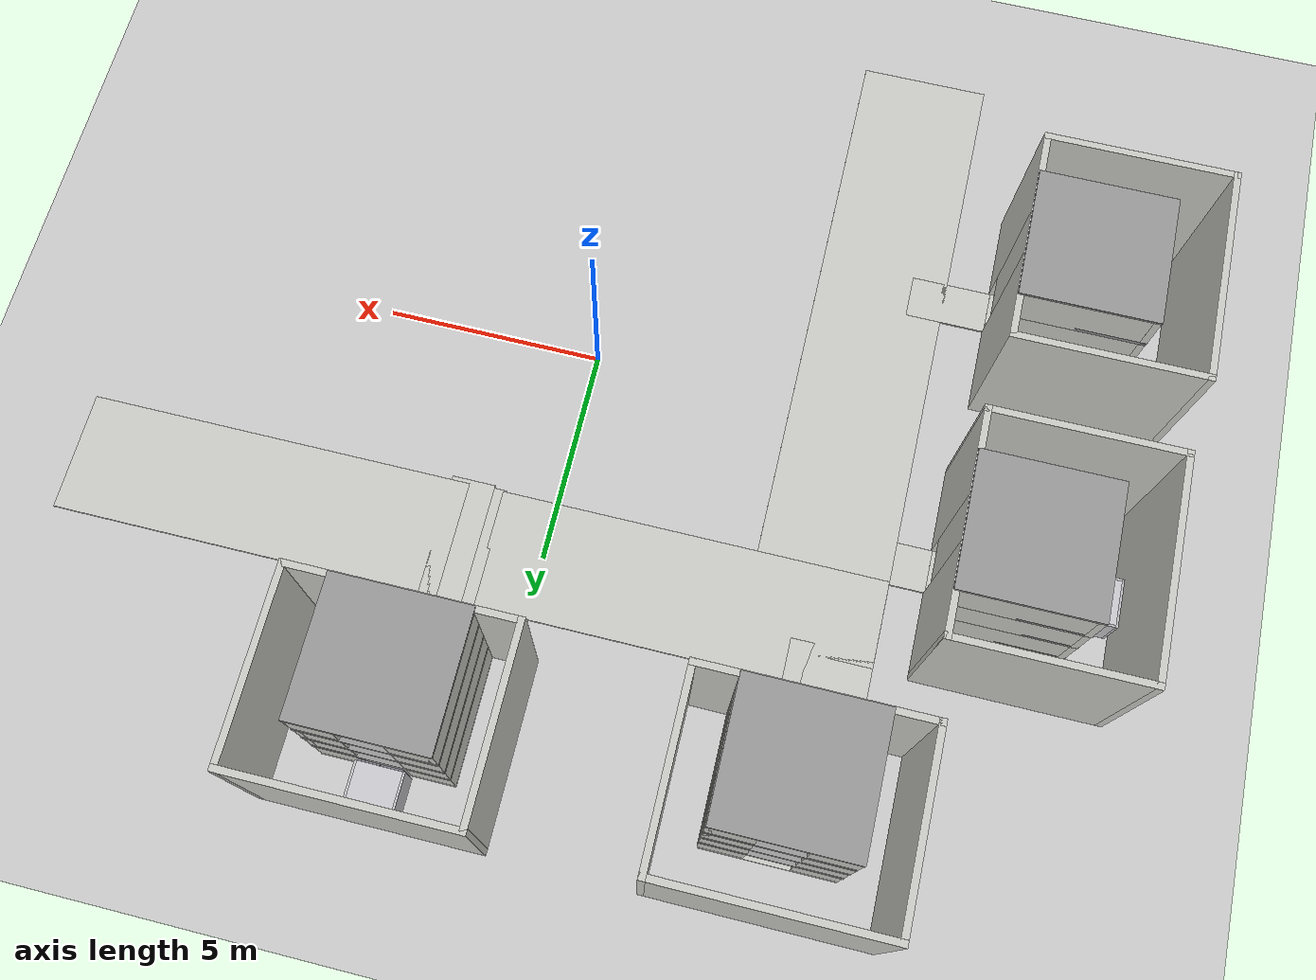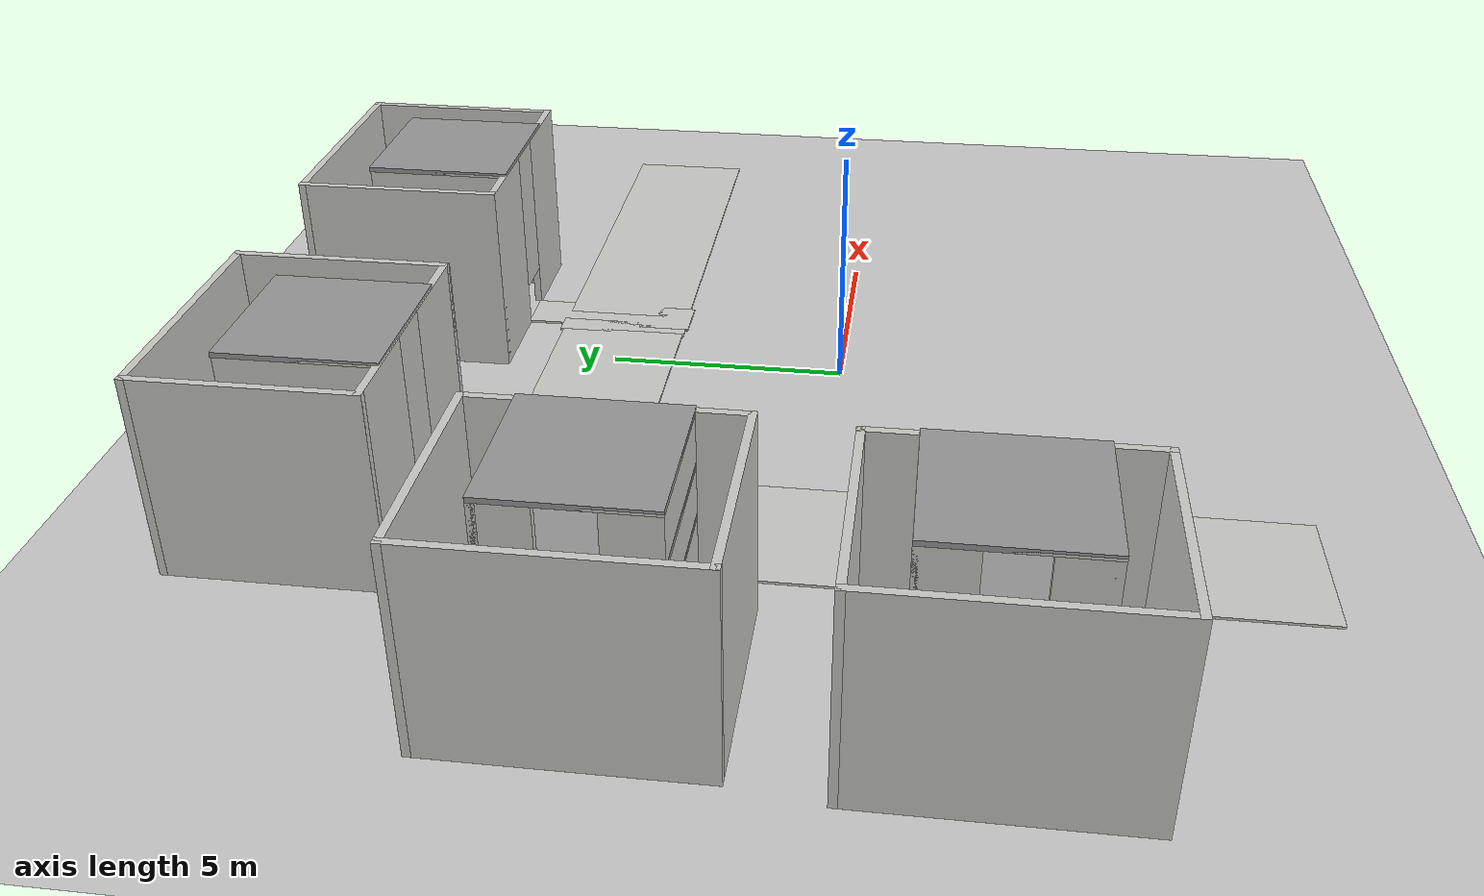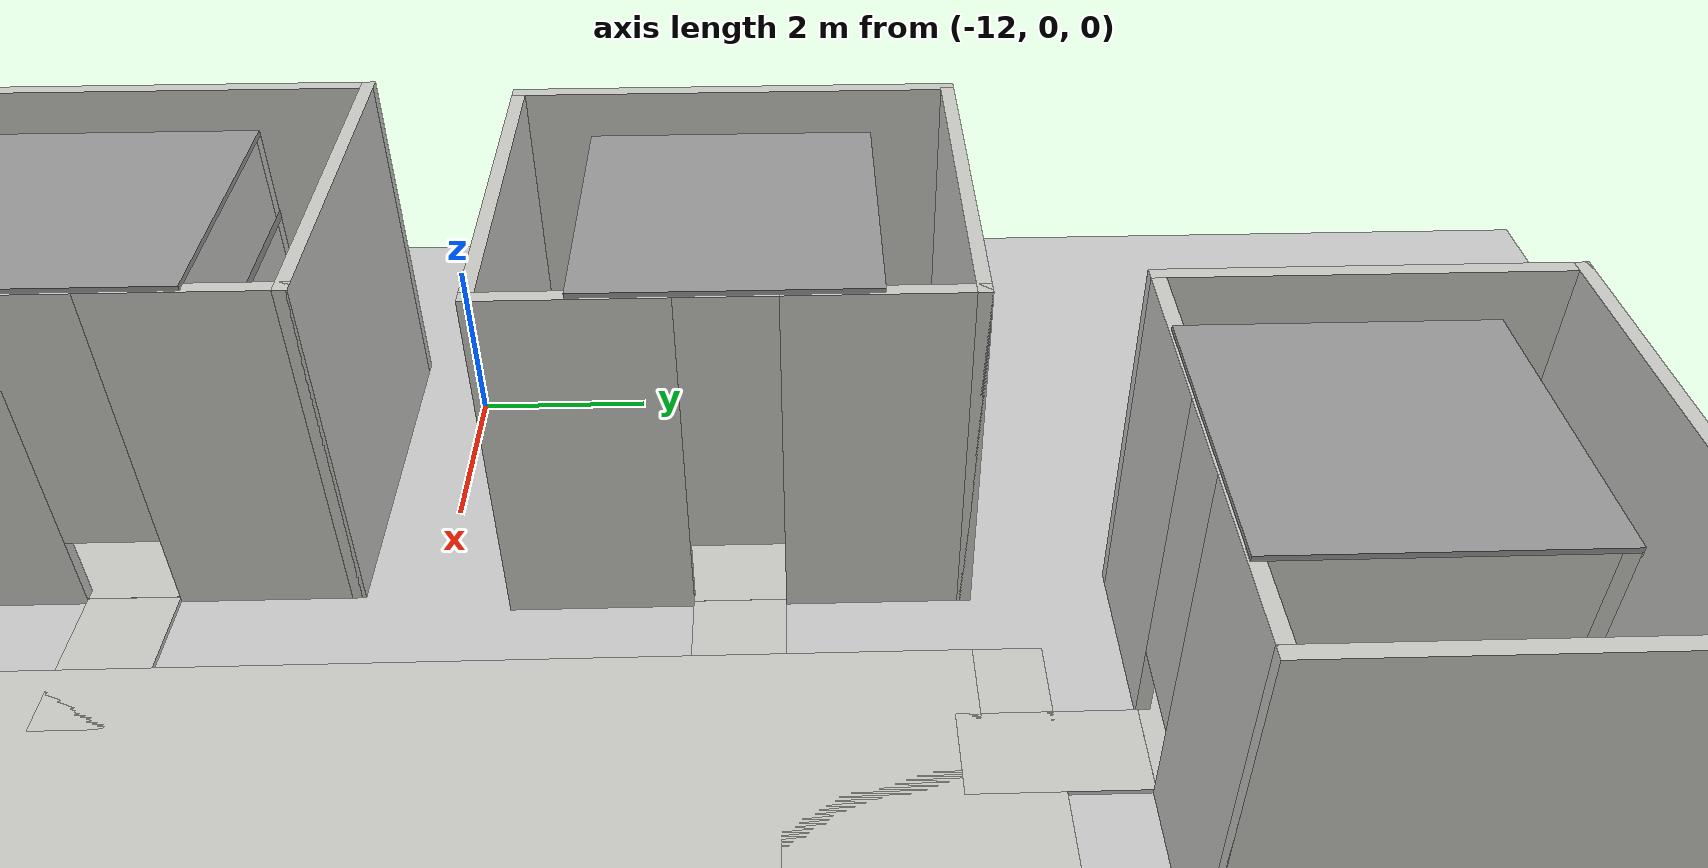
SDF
<sdf version="1.7">
 <world name="default">
  <light name="sun" type="directional">
   <pose>0 0 10 0 -0 0</pose>
   <diffuse>0.8 0.8 0.8 1</diffuse>
   <specular>0.2 0.2 0.2 1</specular>
   <attenuation>
    <range>1000</range>
    <constant>0.9</constant>
    <linear>0.01</linear>
    <quadratic>0.001</quadratic>
   </attenuation>
   <direction>-0.5 0.1 -0.9</direction>
   <spot><inner_angle>0</inner_angle><outer_angle>0</outer_angle><falloff>0</falloff></spot>
  </light>
  <scene><shadows>0</shadows><ambient>0.4 0.4 0.4 1</ambient><background>0.7 0.7 0.7 1</background></scene>
  <physics type="ode">
   <real_time_update_rate>1000</real_time_update_rate>
   <max_step_size>0.001</max_step_size>
   <real_time_factor>1</real_time_factor>
   <ode>
    <solver>
     <type>quick</type>
     <iters>150</iters>
     <precon_iters>0</precon_iters>
     <sor>1.4</sor>
     <use_dynamic_moi_rescaling>1</use_dynamic_moi_rescaling>
    </solver>
    <constraints>
     <cfm>1e-05</cfm>
     <erp>0.2</erp>
     <contact_max_correcting_vel>2000</contact_max_correcting_vel>
     <contact_surface_layer>0.01</contact_surface_layer>
    </constraints>
   </ode>
  </physics>
  <gravity>0 0 -9.8</gravity>
  <magnetic_field>6e-06 2.3e-05 -4.2e-05</magnetic_field>
  <atmosphere type="adiabatic"/>
  <audio><device>default</device></audio>
  <spherical_coordinates>
   <surface_model>EARTH_WGS84</surface_model>
   <latitude_deg>0</latitude_deg>
   <longitude_deg>0</longitude_deg>
   <elevation>0</elevation>
   <heading_deg>0</heading_deg>
  </spherical_coordinates>
  <model name="ground_plane">
   <static>1</static>
   <link name="link">
    <collision name="collision">
     <geometry><plane><normal>0 0 1</normal><size>100 100</size></plane></geometry>
     <surface><friction><ode><mu>100</mu><mu2>50</mu2></ode></friction></surface>
    </collision>
    <visual name="visual">
     <cast_shadows>0</cast_shadows>
     <geometry><plane><normal>0 0 1</normal><size>100 100</size></plane></geometry>
     <material>
      <script><uri>file://media/materials/scripts/gazebo.material</uri><name>Gazebo/Grey</name></script>
     </material>
    </visual>
   </link>
   <pose>-9.56672 -8.6074 0 0 -0 0</pose>
  </model>
  <model name="realPath">
   <pose>0.02771 0.80471 0 0 -0 0</pose>
   <link name="Wall_14">
    <collision name="Wall_14_Collision">
     <geometry><box><size>1.5 0.15 2.5</size></box></geometry>
     <pose>0 0 1.25 0 -0 0</pose>
    </collision>
    <pose>-7.9532 -4.57364 0 0 -0 0</pose>
   </link>
   <link name="Wall_15">
    <collision name="Wall_15_Collision">
     <geometry><box><size>0.516659 0.15 2.5</size></box></geometry>
     <pose>0 0 1.25 0 -0 0</pose>
    </collision>
    <pose>-7.2524 -4.75515 0 0 -0 -1.42962</pose>
   </link>
   <link name="Wall_18">
    <collision name="Wall_18_Collision">
     <geometry><box><size>1.5 0.15 2.5</size></box></geometry>
     <pose>0 0 1.25 0 -0 0</pose>
    </collision>
    <pose>-7.95747 -3.7233 0 0 -0 0</pose>
   </link>
   <link name="Wall_2">
    <collision name="Wall_2_Collision">
     <geometry><box><size>2.5 0.15 2.5</size></box></geometry>
     <pose>0 0 1.25 0 -0 0</pose>
    </collision>
    <pose>11.4734 3.98835 0 0 -0 -1.5708</pose>
   </link>
   <link name="Wall_21">
    <collision name="Wall_21_Collision">
     <geometry><box><size>6 0.15 2.5</size></box></geometry>
     <pose>0 0 1.25 0 -0 0</pose>
    </collision>
    <pose>-7.28033 -0.798471 0 0 -0 1.57007</pose>
   </link>
   <link name="Wall_22">
    <collision name="Wall_22_Collision">
     <geometry><box><size>1.27011 0.15 2.5</size></box></geometry>
     <pose>0 0 1.25 0 -0 0</pose>
    </collision>
    <pose>-7.83826 2.12636 0 0 -0 -3.14159</pose>
   </link>
   <link name="Wall_25">
    <collision name="Wall_25_Collision">
     <geometry><box><size>1.27011 0.15 2.5</size></box></geometry>
     <pose>0 0 1.25 0 -0 0</pose>
    </collision>
    <pose>-7.83826 2.97636 0 0 -0 0</pose>
   </link>
   <link name="Wall_26">
    <collision name="Wall_26_Collision">
     <geometry><box><size>2.5 0.15 2.5</size></box></geometry>
     <pose>0 0 1.25 0 -0 0</pose>
    </collision>
    <pose>-7.2782 4.15136 0 0 -0 1.5708</pose>
   </link>
   <link name="Wall_27">
    <collision name="Wall_27_Collision">
     <geometry><box><size>0.75 0.15 2.5</size></box></geometry>
     <pose>0 0 1.25 0 -0 0</pose>
    </collision>
    <pose>-6.9782 5.32636 0 0 -0 0</pose>
   </link>
   <link name="Wall_29">
    <collision name="Wall_29_Collision">
     <geometry><box><size>1.25 0.15 2.5</size></box></geometry>
     <pose>0 0 1.25 0 -0 0</pose>
    </collision>
    <pose>-6.6782 5.87636 0 0 -0 1.5708</pose>
   </link>
   <link name="Wall_3">
    <collision name="Wall_3_Collision">
     <geometry><box><size>16.25 0.15 2.5</size></box></geometry>
     <pose>0 0 1.25 0 -0 0</pose>
    </collision>
    <pose>3.42339 2.81335 0 0 -0 3.14159</pose>
   </link>
   <link name="Wall_31">
    <collision name="Wall_31_Collision">
     <geometry><box><size>1.25 0.15 2.5</size></box></geometry>
     <pose>0 0 1.25 0 -0 0</pose>
    </collision>
    <pose>-5.8282 5.87636 0 0 -0 -1.5708</pose>
   </link>
   <link name="Wall_32">
    <collision name="Wall_32_Collision">
     <geometry><box><size>7.5 0.15 2.5</size></box></geometry>
     <pose>0 0 1.25 0 -0 0</pose>
    </collision>
    <pose>-2.1532 5.32636 0 0 -0 0</pose>
   </link>
   <link name="Wall_36">
    <collision name="Wall_36_Collision">
     <geometry><box><size>9.25 0.15 2.5</size></box></geometry>
     <pose>0 0 1.25 0 -0 0</pose>
    </collision>
    <pose>6.9018 5.33636 0 0 -0 0</pose>
   </link>
   <link name="Wall_37">
    <collision name="Wall_37_Collision">
     <geometry><box><size>0.15 0.15 2.5</size></box></geometry>
     <pose>0 0 1.25 0 -0 0</pose>
    </collision>
    <pose>11.4518 5.32636 0 0 -0 0</pose>
   </link>
   <link name="Wall_39">
    <collision name="Wall_39_Collision">
     <geometry><box><size>0.314435 0.15 2.5</size></box></geometry>
     <pose>0 0 1.25 0 -0 0</pose>
    </collision>
    <pose>11.4626 5.24485 0 0 -0 -1.4391</pose>
   </link>
   <link name="Wall_4">
    <collision name="Wall_4_Collision">
     <geometry><box><size>12.25 0.15 2.5</size></box></geometry>
     <pose>0 0 1.25 0 -0 0</pose>
    </collision>
    <pose>-4.62661 -3.23665 0 0 -0 -1.5708</pose>
   </link>
   <link name="Wall_5">
    <collision name="Wall_5_Collision">
     <geometry><box><size>2.75 0.15 2.5</size></box></geometry>
     <pose>0 0 1.25 0 -0 0</pose>
    </collision>
    <pose>-5.92661 -9.28665 0 0 -0 3.14159</pose>
   </link>
   <link name="Wall_7">
    <collision name="Wall_7_Collision">
     <geometry><box><size>4.5 0.15 2.5</size></box></geometry>
     <pose>0 0 1.25 0 -0 0</pose>
    </collision>
    <pose>-7.22661 -7.11165 0 0 -0 1.5708</pose>
   </link>
   <link name="Wall_8">
    <collision name="Wall_8_Collision">
     <geometry><box><size>0.25 0.15 2.5</size></box></geometry>
     <pose>0 0 1.25 0 -0 0</pose>
    </collision>
    <pose>-7.22661 -4.88665 0 0 -0 1.5708</pose>
   </link>
   <link name="Wall_81">
    <collision name="Wall_81_Collision">
     <geometry><box><size>1.25 0.15 2.5</size></box></geometry>
     <pose>0 0 1.25 0 -0 0</pose>
    </collision>
    <pose>1.5218 5.87636 0 0 -0 1.5708</pose>
   </link>
   <link name="Wall_85">
    <collision name="Wall_85_Collision">
     <geometry><box><size>1.25 0.15 2.5</size></box></geometry>
     <pose>0 0 1.25 0 -0 0</pose>
    </collision>
    <pose>2.3518 5.88636 0 0 -0 1.5708</pose>
   </link>
   <static>1</static>
  </model>
  <model name="indo">
   <pose>0.81327 -0.60537 0 0 -0 0</pose>
   <link name="Wall_12">
    <collision name="Wall_12_Collision">
     <geometry><box><size>9 2.75 0.05</size></box></geometry>
     <pose>0 0 0.025 0 -0 0</pose>
    </collision>
    <visual name="Wall_12_Visual">
     <pose>0 0 0.025 0 -0 0</pose>
     <geometry><box><size>9 2.75 0.05</size></box></geometry>
     <material>
      <script><uri>file://media/materials/scripts/gazebo.material</uri><name>Gazebo/CeilingTiled</name></script>
      <ambient>1 1 1 1</ambient>
     </material>
     <meta><layer>0</layer></meta>
    </visual>
    <pose>5.75239 5.68288 0 0 -0 3.14159</pose>
   </link>
   <link name="Wall_18">
    <collision name="Wall_18_Collision">
     <geometry><box><size>8.9 2.75 0.05</size></box></geometry>
     <pose>0 0 0.025 0 -0 0</pose>
    </collision>
    <visual name="Wall_18_Visual">
     <pose>0 0 0.025 0 -0 0</pose>
     <geometry><box><size>8.9 2.75 0.05</size></box></geometry>
     <material>
      <script><uri>file://media/materials/scripts/gazebo.material</uri><name>Gazebo/CeilingTiled</name></script>
      <ambient>1 1 1 1</ambient>
     </material>
     <meta><layer>0</layer></meta>
    </visual>
    <pose>-3.99159 5.67955 0 0 -0 3.14159</pose>
   </link>
   <link name="Wall_22">
    <collision name="Wall_22_Collision">
     <geometry><box><size>15 3 0.05</size></box></geometry>
     <pose>0 0 0.025 0 -0 0</pose>
    </collision>
    <visual name="Wall_22_Visual">
     <pose>0 0 0.025 0 -0 0</pose>
     <geometry><box><size>15 3 0.05</size></box></geometry>
     <material>
      <script><uri>file://media/materials/scripts/gazebo.material</uri><name>Gazebo/CeilingTiled</name></script>
      <ambient>1 1 1 1</ambient>
     </material>
     <meta><layer>0</layer></meta>
    </visual>
    <pose>-6.94474 -1.17738 0 0 -0 -1.5708</pose>
   </link>
   <static>1</static>
  </model>
  <model name="indo2">
   <pose>-3.08902 1.74007 0 0 -0 0</pose>
   <link name="Wall_10">
    <collision name="Wall_10_Collision">
     <geometry><box><size>3.7 1 0.05</size></box></geometry>
     <pose>0 0 0.025 0 -0 0</pose>
    </collision>
    <visual name="Wall_10_Visual">
     <pose>0 0 0.025 0 -0 0</pose>
     <geometry><box><size>3.7 1 0.05</size></box></geometry>
     <material>
      <script><uri>file://media/materials/scripts/gazebo.material</uri><name>Gazebo/CeilingTiled</name></script>
      <ambient>1 1 1 1</ambient>
     </material>
     <meta><layer>0</layer></meta>
    </visual>
    <pose>5.07653 3.72055 0 0 -0 -1.5708</pose>
   </link>
   <link name="Wall_14">
    <collision name="Wall_14_Collision">
     <geometry><box><size>1.85 1 0.05</size></box></geometry>
     <pose>0 0 0.025 0 -0 0</pose>
    </collision>
    <visual name="Wall_14_Visual">
     <pose>0 0 0.025 0 -0 0</pose>
     <geometry><box><size>1.85 1 0.05</size></box></geometry>
     <material>
      <script><uri>file://media/materials/scripts/gazebo.material</uri><name>Gazebo/CeilingTiled</name></script>
      <ambient>1 1 1 1</ambient>
     </material>
     <meta><layer>0</layer></meta>
    </visual>
    <pose>-3.16858 4.64438 0 0 -0 -1.5708</pose>
   </link>
   <link name="Wall_17">
    <collision name="Wall_17_Collision">
     <geometry><box><size>1.01 1 0.05</size></box></geometry>
     <pose>0 0 0.025 0 -0 0</pose>
    </collision>
    <visual name="Wall_17_Visual">
     <pose>0 0 0.025 0 -0 0</pose>
     <geometry><box><size>1.01 1 0.05</size></box></geometry>
     <material>
      <script><uri>file://media/materials/scripts/gazebo.material</uri><name>Gazebo/CeilingTiled</name></script>
      <ambient>1 1 1 1</ambient>
     </material>
     <meta><layer>0</layer></meta>
    </visual>
    <pose>-4.83677 1.52639 0 0 -0 3.14159</pose>
   </link>
   <link name="Wall_20">
    <collision name="Wall_20_Collision">
     <geometry><box><size>1.85 1 0.05</size></box></geometry>
     <pose>0 0 0.025 0 -0 0</pose>
    </collision>
    <visual name="Wall_20_Visual">
     <pose>0 0 0.025 0 -0 0</pose>
     <geometry><box><size>1.85 1 0.05</size></box></geometry>
     <material>
      <script><uri>file://media/materials/scripts/gazebo.material</uri><name>Gazebo/CeilingTiled</name></script>
      <ambient>1 1 1 1</ambient>
     </material>
     <meta><layer>0</layer></meta>
    </visual>
    <pose>-4.65153 -5.07055 0 0 -0 0</pose>
   </link>
   <static>1</static>
  </model>
  <model name="Bbang">
   <pose>0.80818 3.5119 0 0 -0 0</pose>
   <link name="Wall_23">
    <collision name="Wall_23_Collision">
     <geometry><box><size>2.85 0.5 0.05</size></box></geometry>
     <pose>0 0 0.025 0 -0 0</pose>
    </collision>
    <visual name="Wall_23_Visual">
     <pose>0 0 0.025 0 -0 0</pose>
     <geometry><box><size>2.85 0.5 0.05</size></box></geometry>
     <material>
      <script><uri>file://media/materials/scripts/gazebo.material</uri><name>Gazebo/CeilingTiled</name></script>
      <ambient>1 1 1 1</ambient>
     </material>
     <meta><layer>0</layer></meta>
    </visual>
    <pose>0.6415 1.5825 0 0 -0 1.5708</pose>
   </link>
   <static>1</static>
  </model>
  <model name="apart3">
   <pose>-8.04894 1.2794 0 0 0 -1.57079</pose>
   <link name="Floor_10">
    <collision name="Floor_10_Collision">
     <geometry><box><size>3.005 3.015 0.1</size></box></geometry>
     <pose>0 0 0.05 0 -0 0</pose>
    </collision>
    <visual name="Floor_10_Visual">
     <pose>0 0 0.05 0 -0 0</pose>
     <geometry><box><size>3.005 3.015 0.1</size></box></geometry>
     <material>
      <script><uri>file://media/materials/scripts/gazebo.material</uri><name>Gazebo/Grey</name></script>
      <ambient>1 1 1 1</ambient>
     </material>
     <meta><layer>2</layer></meta>
    </visual>
    <pose>-1.995 -1.885 2 0 -0 0</pose>
   </link>
   <link name="Floor_11">
    <collision name="Floor_11_Collision">
     <geometry><box><size>3.005 3.015 0.1</size></box></geometry>
     <pose>0 0 0.05 0 -0 0</pose>
    </collision>
    <visual name="Floor_11_Visual">
     <pose>0 0 0.05 0 -0 0</pose>
     <geometry><box><size>3.005 3.015 0.1</size></box></geometry>
     <material>
      <script><uri>file://media/materials/scripts/gazebo.material</uri><name>Gazebo/Grey</name></script>
      <ambient>1 1 1 1</ambient>
     </material>
     <meta><layer>3</layer></meta>
    </visual>
    <pose>-1.995 -1.885 3 0 -0 0</pose>
   </link>
   <link name="Floor_12">
    <collision name="Floor_12_Collision">
     <geometry><box><size>3 3.01 0.1</size></box></geometry>
     <pose>0 0 0.05 0 -0 0</pose>
    </collision>
    <visual name="Floor_12_Visual">
     <pose>0 0 0.05 0 -0 0</pose>
     <geometry><box><size>3 3.01 0.1</size></box></geometry>
     <material>
      <script><uri>file://media/materials/scripts/gazebo.material</uri><name>Gazebo/Grey</name></script>
      <ambient>1 1 1 1</ambient>
     </material>
     <meta><layer>4</layer></meta>
    </visual>
    <pose>-1.9925 -1.8875 4 0 -0 0</pose>
   </link>
   <link name="Floor_9">
    <collision name="Floor_9_Collision">
     <geometry><box><size>3.005 3.015 0.1</size></box></geometry>
     <pose>0 0 0.05 0 -0 0</pose>
    </collision>
    <visual name="Floor_9_Visual">
     <pose>0 0 0.05 0 -0 0</pose>
     <geometry><box><size>3.005 3.015 0.1</size></box></geometry>
     <material>
      <script><uri>file://media/materials/scripts/gazebo.material</uri><name>Gazebo/Grey</name></script>
      <ambient>1 1 1 1</ambient>
     </material>
     <meta><layer>1</layer></meta>
    </visual>
    <pose>-1.995 -1.885 1 0 -0 0</pose>
   </link>
   <link name="Wall_100">
    <collision name="Wall_100_Collision">
     <geometry><box><size>3 0.15 1.05</size></box></geometry>
     <pose>0 0 0.525 0 -0 0</pose>
    </collision>
    <visual name="Wall_100_Visual">
     <pose>0 0 0.525 0 -0 0</pose>
     <geometry><box><size>3 0.15 1.05</size></box></geometry>
     <material>
      <script><uri>file://media/materials/scripts/gazebo.material</uri><name>Gazebo/CeilingTiled</name></script>
      <ambient>1 1 1 1</ambient>
     </material>
     <meta><layer>3</layer></meta>
    </visual>
    <pose>-0.5725 -1.8775 3 0 -0 1.5708</pose>
   </link>
   <link name="Wall_101">
    <collision name="Wall_101_Collision">
     <geometry><box><size>3 0.15 1.05</size></box></geometry>
     <pose>0 0 0.525 0 -0 0</pose>
    </collision>
    <visual name="Wall_101_Visual">
     <pose>0 0 0.525 0 -0 0</pose>
     <geometry><box><size>3 0.15 1.05</size></box></geometry>
     <material>
      <script><uri>file://media/materials/scripts/gazebo.material</uri><name>Gazebo/CeilingTiled</name></script>
      <ambient>1 1 1 1</ambient>
     </material>
     <meta><layer>3</layer></meta>
    </visual>
    <pose>-3.4225 -1.8775 3 0 -0 1.5708</pose>
   </link>
   <link name="Wall_102">
    <collision name="Wall_102_Collision">
     <geometry><box><size>1 0.15 1.05</size></box></geometry>
     <pose>0 0 0.525 0 -0 0</pose>
    </collision>
    <visual name="Wall_102_Visual">
     <pose>0 0 0.525 0 -0 0</pose>
     <geometry><box><size>1 0.15 1.05</size></box></geometry>
     <material>
      <script><uri>file://media/materials/scripts/gazebo.material</uri><name>Gazebo/CeilingTiled</name></script>
      <ambient>1 1 1 1</ambient>
     </material>
     <meta><layer>3</layer></meta>
    </visual>
    <pose>-2.9975 -3.3025 3 0 -0 0</pose>
   </link>
   <link name="Wall_103">
    <collision name="Wall_103_Collision">
     <geometry><box><size>1 0.15 1.05</size></box></geometry>
     <pose>0 0 0.525 0 -0 0</pose>
    </collision>
    <visual name="Wall_103_Visual">
     <pose>0 0 0.525 0 -0 0</pose>
     <geometry><box><size>1 0.15 1.05</size></box></geometry>
     <material>
      <script><uri>file://media/materials/scripts/gazebo.material</uri><name>Gazebo/CeilingTiled</name></script>
      <ambient>1 1 1 1</ambient>
     </material>
     <meta><layer>3</layer></meta>
    </visual>
    <pose>-0.9975 -3.3025 3 0 -0 3.14159</pose>
   </link>
   <link name="Wall_104">
    <collision name="Wall_104_Collision">
     <geometry><box><size>3.01 3 0.05</size></box></geometry>
     <pose>0 0 0.025 0 -0 0</pose>
    </collision>
    <visual name="Wall_104_Visual">
     <pose>0 0 0.025 0 -0 0</pose>
     <geometry><box><size>3.01 3 0.05</size></box></geometry>
     <material>
      <script><uri>file://media/materials/scripts/gazebo.material</uri><name>Gazebo/CeilingTiled</name></script>
      <ambient>1 1 1 1</ambient>
     </material>
     <meta><layer>4</layer></meta>
    </visual>
    <pose>-1.9925 -1.8875 4 0 -0 -1.5708</pose>
   </link>
   <link name="Wall_117">
    <pose>-1.9975 -0.4325 0 0 -0 0</pose>
    <visual name="Wall_117_Visual_0">
     <pose>-1.4975 0 2.025 0 -0 0</pose>
     <geometry><box><size>2.005 0.15 4.05</size></box></geometry>
     <material>
      <script><uri>file://media/materials/scripts/gazebo.material</uri><name>Gazebo/CeilingTiled</name></script>
      <ambient>0.760784 0.662745 0.627451 1</ambient>
     </material>
     <meta><layer>0</layer></meta>
    </visual>
    <collision name="Wall_117_Collision_0">
     <geometry><box><size>2.005 0.15 4.05</size></box></geometry>
     <pose>-1.4975 0 2.025 0 -0 0</pose>
    </collision>
    <visual name="Wall_117_Visual_1">
     <pose>1.5025 0 2.025 0 -0 0</pose>
     <geometry><box><size>1.995 0.15 4.05</size></box></geometry>
     <material>
      <script><uri>file://media/materials/scripts/gazebo.material</uri><name>Gazebo/CeilingTiled</name></script>
      <ambient>0.760784 0.662745 0.627451 1</ambient>
     </material>
     <meta><layer>0</layer></meta>
    </visual>
    <collision name="Wall_117_Collision_1">
     <geometry><box><size>1.995 0.15 4.05</size></box></geometry>
     <pose>1.5025 0 2.025 0 -0 0</pose>
    </collision>
    <visual name="Wall_117_Visual_2">
     <pose>0.005 0 2.475 0 -0 0</pose>
     <geometry><box><size>1 0.15 3.15</size></box></geometry>
     <material>
      <script><uri>file://media/materials/scripts/gazebo.material</uri><name>Gazebo/CeilingTiled</name></script>
      <ambient>0.760784 0.662745 0.627451 1</ambient>
     </material>
     <meta><layer>0</layer></meta>
    </visual>
    <collision name="Wall_117_Collision_2">
     <geometry><box><size>1 0.15 3.15</size></box></geometry>
     <pose>0.005 0 2.475 0 -0 0</pose>
    </collision>
   </link>
   <link name="Wall_118">
    <collision name="Wall_118_Collision">
     <geometry><box><size>4.25 0.15 4.05</size></box></geometry>
     <pose>0 0 2.025 0 -0 0</pose>
    </collision>
    <visual name="Wall_118_Visual">
     <pose>0 0 2.025 0 -0 0</pose>
     <geometry><box><size>4.25 0.15 4.05</size></box></geometry>
     <material>
      <script><uri>file://media/materials/scripts/gazebo.material</uri><name>Gazebo/CeilingTiled</name></script>
      <ambient>0.760784 0.662745 0.627451 1</ambient>
     </material>
     <meta><layer>0</layer></meta>
    </visual>
    <pose>0.4275 -2.4825 0 0 -0 -1.5708</pose>
   </link>
   <link name="Wall_119">
    <collision name="Wall_119_Collision">
     <geometry><box><size>5 0.15 4.05</size></box></geometry>
     <pose>0 0 2.025 0 -0 0</pose>
    </collision>
    <visual name="Wall_119_Visual">
     <pose>0 0 2.025 0 -0 0</pose>
     <geometry><box><size>5 0.15 4.05</size></box></geometry>
     <material>
      <script><uri>file://media/materials/scripts/gazebo.material</uri><name>Gazebo/CeilingTiled</name></script>
      <ambient>0.760784 0.662745 0.627451 1</ambient>
     </material>
     <meta><layer>0</layer></meta>
    </visual>
    <pose>-1.9975 -4.5325 0 0 -0 3.14159</pose>
   </link>
   <link name="Wall_120">
    <collision name="Wall_120_Collision">
     <geometry><box><size>4.25 0.15 4.05</size></box></geometry>
     <pose>0 0 2.025 0 -0 0</pose>
    </collision>
    <visual name="Wall_120_Visual">
     <pose>0 0 2.025 0 -0 0</pose>
     <geometry><box><size>4.25 0.15 4.05</size></box></geometry>
     <material>
      <script><uri>file://media/materials/scripts/gazebo.material</uri><name>Gazebo/CeilingTiled</name></script>
      <ambient>0.760784 0.662745 0.627451 1</ambient>
     </material>
     <meta><layer>0</layer></meta>
    </visual>
    <pose>-4.4225 -2.4825 0 0 -0 1.5708</pose>
   </link>
   <link name="Wall_71">
    <collision name="Wall_71_Collision">
     <geometry><box><size>3.01 3 0.05</size></box></geometry>
     <pose>0 0 0.025 0 -0 0</pose>
    </collision>
    <visual name="Wall_71_Visual">
     <pose>0 0 0.025 0 -0 0</pose>
     <geometry><box><size>3.01 3 0.05</size></box></geometry>
     <material>
      <script><uri>file://media/materials/scripts/gazebo.material</uri><name>Gazebo/CeilingTiled</name></script>
      <ambient>1 1 1 1</ambient>
     </material>
     <meta><layer>0</layer></meta>
    </visual>
    <pose>-1.9925 -1.8875 0 0 -0 -1.5708</pose>
   </link>
   <link name="Wall_73">
    <collision name="Wall_73_Collision">
     <geometry><box><size>3 0.15 1</size></box></geometry>
     <pose>0 0 0.5 0 -0 0</pose>
    </collision>
    <visual name="Wall_73_Visual">
     <pose>0 0 0.5 0 -0 0</pose>
     <geometry><box><size>3 0.15 1</size></box></geometry>
     <material>
      <script><uri>file://media/materials/scripts/gazebo.material</uri><name>Gazebo/CeilingTiled</name></script>
      <ambient>1 1 1 1</ambient>
     </material>
     <meta><layer>0</layer></meta>
    </visual>
    <pose>-0.5725 -1.8775 0 0 -0 1.5708</pose>
   </link>
   <link name="Wall_75">
    <collision name="Wall_75_Collision">
     <geometry><box><size>3 0.15 1</size></box></geometry>
     <pose>0 0 0.5 0 -0 0</pose>
    </collision>
    <visual name="Wall_75_Visual">
     <pose>0 0 0.5 0 -0 0</pose>
     <geometry><box><size>3 0.15 1</size></box></geometry>
     <material>
      <script><uri>file://media/materials/scripts/gazebo.material</uri><name>Gazebo/CeilingTiled</name></script>
      <ambient>1 1 1 1</ambient>
     </material>
     <meta><layer>0</layer></meta>
    </visual>
    <pose>-3.4225 -1.8775 0 0 -0 1.5708</pose>
   </link>
   <link name="Wall_85">
    <collision name="Wall_85_Collision">
     <geometry><box><size>1 0.15 1</size></box></geometry>
     <pose>0 0 0.5 0 -0 0</pose>
    </collision>
    <visual name="Wall_85_Visual">
     <pose>0 0 0.5 0 -0 0</pose>
     <geometry><box><size>1 0.15 1</size></box></geometry>
     <material>
      <script><uri>file://media/materials/scripts/gazebo.material</uri><name>Gazebo/CeilingTiled</name></script>
      <ambient>1 1 1 1</ambient>
     </material>
     <meta><layer>0</layer></meta>
    </visual>
    <pose>-2.9975 -3.3025 0 0 -0 0</pose>
   </link>
   <link name="Wall_87">
    <collision name="Wall_87_Collision">
     <geometry><box><size>1 0.15 1</size></box></geometry>
     <pose>0 0 0.5 0 -0 0</pose>
    </collision>
    <visual name="Wall_87_Visual">
     <pose>0 0 0.5 0 -0 0</pose>
     <geometry><box><size>1 0.15 1</size></box></geometry>
     <material>
      <script><uri>file://media/materials/scripts/gazebo.material</uri><name>Gazebo/CeilingTiled</name></script>
      <ambient>1 1 1 1</ambient>
     </material>
     <meta><layer>0</layer></meta>
    </visual>
    <pose>-0.9975 -3.3025 0 0 -0 3.14159</pose>
   </link>
   <link name="Wall_89">
    <collision name="Wall_89_Collision">
     <geometry><box><size>3.01 3 0.05</size></box></geometry>
     <pose>0 0 0.025 0 -0 0</pose>
    </collision>
    <visual name="Wall_89_Visual">
     <pose>0 0 0.025 0 -0 0</pose>
     <geometry><box><size>3.01 3 0.05</size></box></geometry>
     <material>
      <script><uri>file://media/materials/scripts/gazebo.material</uri><name>Gazebo/CeilingTiled</name></script>
      <ambient>1 1 1 1</ambient>
     </material>
     <meta><layer>1</layer></meta>
    </visual>
    <pose>-1.9925 -1.8875 1 0 -0 -1.5708</pose>
   </link>
   <link name="Wall_90">
    <collision name="Wall_90_Collision">
     <geometry><box><size>3 0.15 1</size></box></geometry>
     <pose>0 0 0.5 0 -0 0</pose>
    </collision>
    <visual name="Wall_90_Visual">
     <pose>0 0 0.5 0 -0 0</pose>
     <geometry><box><size>3 0.15 1</size></box></geometry>
     <material>
      <script><uri>file://media/materials/scripts/gazebo.material</uri><name>Gazebo/CeilingTiled</name></script>
      <ambient>1 1 1 1</ambient>
     </material>
     <meta><layer>1</layer></meta>
    </visual>
    <pose>-0.5725 -1.8775 1 0 -0 1.5708</pose>
   </link>
   <link name="Wall_91">
    <collision name="Wall_91_Collision">
     <geometry><box><size>3 0.15 1</size></box></geometry>
     <pose>0 0 0.5 0 -0 0</pose>
    </collision>
    <visual name="Wall_91_Visual">
     <pose>0 0 0.5 0 -0 0</pose>
     <geometry><box><size>3 0.15 1</size></box></geometry>
     <material>
      <script><uri>file://media/materials/scripts/gazebo.material</uri><name>Gazebo/CeilingTiled</name></script>
      <ambient>1 1 1 1</ambient>
     </material>
     <meta><layer>1</layer></meta>
    </visual>
    <pose>-3.4225 -1.8775 1 0 -0 1.5708</pose>
   </link>
   <link name="Wall_92">
    <collision name="Wall_92_Collision">
     <geometry><box><size>1 0.15 1</size></box></geometry>
     <pose>0 0 0.5 0 -0 0</pose>
    </collision>
    <visual name="Wall_92_Visual">
     <pose>0 0 0.5 0 -0 0</pose>
     <geometry><box><size>1 0.15 1</size></box></geometry>
     <material>
      <script><uri>file://media/materials/scripts/gazebo.material</uri><name>Gazebo/CeilingTiled</name></script>
      <ambient>1 1 1 1</ambient>
     </material>
     <meta><layer>1</layer></meta>
    </visual>
    <pose>-2.9975 -3.3025 1 0 -0 0</pose>
   </link>
   <link name="Wall_93">
    <collision name="Wall_93_Collision">
     <geometry><box><size>1 0.15 1</size></box></geometry>
     <pose>0 0 0.5 0 -0 0</pose>
    </collision>
    <visual name="Wall_93_Visual">
     <pose>0 0 0.5 0 -0 0</pose>
     <geometry><box><size>1 0.15 1</size></box></geometry>
     <material>
      <script><uri>file://media/materials/scripts/gazebo.material</uri><name>Gazebo/CeilingTiled</name></script>
      <ambient>1 1 1 1</ambient>
     </material>
     <meta><layer>1</layer></meta>
    </visual>
    <pose>-0.9975 -3.3025 1 0 -0 3.14159</pose>
   </link>
   <link name="Wall_94">
    <collision name="Wall_94_Collision">
     <geometry><box><size>3.01 3 0.05</size></box></geometry>
     <pose>0 0 0.025 0 -0 0</pose>
    </collision>
    <visual name="Wall_94_Visual">
     <pose>0 0 0.025 0 -0 0</pose>
     <geometry><box><size>3.01 3 0.05</size></box></geometry>
     <material>
      <script><uri>file://media/materials/scripts/gazebo.material</uri><name>Gazebo/CeilingTiled</name></script>
      <ambient>1 1 1 1</ambient>
     </material>
     <meta><layer>2</layer></meta>
    </visual>
    <pose>-1.9925 -1.8875 2 0 -0 -1.5708</pose>
   </link>
   <link name="Wall_95">
    <collision name="Wall_95_Collision">
     <geometry><box><size>3 0.15 1</size></box></geometry>
     <pose>0 0 0.5 0 -0 0</pose>
    </collision>
    <visual name="Wall_95_Visual">
     <pose>0 0 0.5 0 -0 0</pose>
     <geometry><box><size>3 0.15 1</size></box></geometry>
     <material>
      <script><uri>file://media/materials/scripts/gazebo.material</uri><name>Gazebo/CeilingTiled</name></script>
      <ambient>1 1 1 1</ambient>
     </material>
     <meta><layer>2</layer></meta>
    </visual>
    <pose>-0.5725 -1.8775 2 0 -0 1.5708</pose>
   </link>
   <link name="Wall_96">
    <collision name="Wall_96_Collision">
     <geometry><box><size>3 0.15 1</size></box></geometry>
     <pose>0 0 0.5 0 -0 0</pose>
    </collision>
    <visual name="Wall_96_Visual">
     <pose>0 0 0.5 0 -0 0</pose>
     <geometry><box><size>3 0.15 1</size></box></geometry>
     <material>
      <script><uri>file://media/materials/scripts/gazebo.material</uri><name>Gazebo/CeilingTiled</name></script>
      <ambient>1 1 1 1</ambient>
     </material>
     <meta><layer>2</layer></meta>
    </visual>
    <pose>-3.4225 -1.8775 2 0 -0 1.5708</pose>
   </link>
   <link name="Wall_97">
    <collision name="Wall_97_Collision">
     <geometry><box><size>1 0.15 1</size></box></geometry>
     <pose>0 0 0.5 0 -0 0</pose>
    </collision>
    <visual name="Wall_97_Visual">
     <pose>0 0 0.5 0 -0 0</pose>
     <geometry><box><size>1 0.15 1</size></box></geometry>
     <material>
      <script><uri>file://media/materials/scripts/gazebo.material</uri><name>Gazebo/CeilingTiled</name></script>
      <ambient>1 1 1 1</ambient>
     </material>
     <meta><layer>2</layer></meta>
    </visual>
    <pose>-2.9975 -3.3025 2 0 -0 0</pose>
   </link>
   <link name="Wall_98">
    <collision name="Wall_98_Collision">
     <geometry><box><size>1 0.15 1</size></box></geometry>
     <pose>0 0 0.5 0 -0 0</pose>
    </collision>
    <visual name="Wall_98_Visual">
     <pose>0 0 0.5 0 -0 0</pose>
     <geometry><box><size>1 0.15 1</size></box></geometry>
     <material>
      <script><uri>file://media/materials/scripts/gazebo.material</uri><name>Gazebo/CeilingTiled</name></script>
      <ambient>1 1 1 1</ambient>
     </material>
     <meta><layer>2</layer></meta>
    </visual>
    <pose>-0.9975 -3.3025 2 0 -0 3.14159</pose>
   </link>
   <link name="Wall_99">
    <collision name="Wall_99_Collision">
     <geometry><box><size>3.01 3 0.05</size></box></geometry>
     <pose>0 0 0.025 0 -0 0</pose>
    </collision>
    <visual name="Wall_99_Visual">
     <pose>0 0 0.025 0 -0 0</pose>
     <geometry><box><size>3.01 3 0.05</size></box></geometry>
     <material>
      <script><uri>file://media/materials/scripts/gazebo.material</uri><name>Gazebo/CeilingTiled</name></script>
      <ambient>1 1 1 1</ambient>
     </material>
     <meta><layer>3</layer></meta>
    </visual>
    <pose>-1.9925 -1.8875 3 0 -0 -1.5708</pose>
   </link>
   <static>1</static>
  </model>
  <model name="apart2">
   <pose>-8.24836 6.92736 0 0 -0 3.14159</pose>
   <link name="Floor_10">
    <collision name="Floor_10_Collision">
     <geometry><box><size>3.005 3.015 0.1</size></box></geometry>
     <pose>0 0 0.05 0 -0 0</pose>
    </collision>
    <visual name="Floor_10_Visual">
     <pose>0 0 0.05 0 -0 0</pose>
     <geometry><box><size>3.005 3.015 0.1</size></box></geometry>
     <material>
      <script><uri>file://media/materials/scripts/gazebo.material</uri><name>Gazebo/Grey</name></script>
      <ambient>1 1 1 1</ambient>
     </material>
     <meta><layer>2</layer></meta>
    </visual>
    <pose>-1.995 -1.885 2 0 -0 0</pose>
   </link>
   <link name="Floor_11">
    <collision name="Floor_11_Collision">
     <geometry><box><size>3.005 3.015 0.1</size></box></geometry>
     <pose>0 0 0.05 0 -0 0</pose>
    </collision>
    <visual name="Floor_11_Visual">
     <pose>0 0 0.05 0 -0 0</pose>
     <geometry><box><size>3.005 3.015 0.1</size></box></geometry>
     <material>
      <script><uri>file://media/materials/scripts/gazebo.material</uri><name>Gazebo/Grey</name></script>
      <ambient>1 1 1 1</ambient>
     </material>
     <meta><layer>3</layer></meta>
    </visual>
    <pose>-1.995 -1.885 3 0 -0 0</pose>
   </link>
   <link name="Floor_12">
    <collision name="Floor_12_Collision">
     <geometry><box><size>3 3.01 0.1</size></box></geometry>
     <pose>0 0 0.05 0 -0 0</pose>
    </collision>
    <visual name="Floor_12_Visual">
     <pose>0 0 0.05 0 -0 0</pose>
     <geometry><box><size>3 3.01 0.1</size></box></geometry>
     <material>
      <script><uri>file://media/materials/scripts/gazebo.material</uri><name>Gazebo/Grey</name></script>
      <ambient>1 1 1 1</ambient>
     </material>
     <meta><layer>4</layer></meta>
    </visual>
    <pose>-1.9925 -1.8875 4 0 -0 0</pose>
   </link>
   <link name="Floor_9">
    <collision name="Floor_9_Collision">
     <geometry><box><size>3.005 3.015 0.1</size></box></geometry>
     <pose>0 0 0.05 0 -0 0</pose>
    </collision>
    <visual name="Floor_9_Visual">
     <pose>0 0 0.05 0 -0 0</pose>
     <geometry><box><size>3.005 3.015 0.1</size></box></geometry>
     <material>
      <script><uri>file://media/materials/scripts/gazebo.material</uri><name>Gazebo/Grey</name></script>
      <ambient>1 1 1 1</ambient>
     </material>
     <meta><layer>1</layer></meta>
    </visual>
    <pose>-1.995 -1.885 1 0 -0 0</pose>
   </link>
   <link name="Wall_100">
    <collision name="Wall_100_Collision">
     <geometry><box><size>3 0.15 1.05</size></box></geometry>
     <pose>0 0 0.525 0 -0 0</pose>
    </collision>
    <visual name="Wall_100_Visual">
     <pose>0 0 0.525 0 -0 0</pose>
     <geometry><box><size>3 0.15 1.05</size></box></geometry>
     <material>
      <script><uri>file://media/materials/scripts/gazebo.material</uri><name>Gazebo/CeilingTiled</name></script>
      <ambient>1 1 1 1</ambient>
     </material>
     <meta><layer>3</layer></meta>
    </visual>
    <pose>-0.5725 -1.8775 3 0 -0 1.5708</pose>
   </link>
   <link name="Wall_101">
    <collision name="Wall_101_Collision">
     <geometry><box><size>3 0.15 1.05</size></box></geometry>
     <pose>0 0 0.525 0 -0 0</pose>
    </collision>
    <visual name="Wall_101_Visual">
     <pose>0 0 0.525 0 -0 0</pose>
     <geometry><box><size>3 0.15 1.05</size></box></geometry>
     <material>
      <script><uri>file://media/materials/scripts/gazebo.material</uri><name>Gazebo/CeilingTiled</name></script>
      <ambient>1 1 1 1</ambient>
     </material>
     <meta><layer>3</layer></meta>
    </visual>
    <pose>-3.4225 -1.8775 3 0 -0 1.5708</pose>
   </link>
   <link name="Wall_102">
    <collision name="Wall_102_Collision">
     <geometry><box><size>1 0.15 1.05</size></box></geometry>
     <pose>0 0 0.525 0 -0 0</pose>
    </collision>
    <visual name="Wall_102_Visual">
     <pose>0 0 0.525 0 -0 0</pose>
     <geometry><box><size>1 0.15 1.05</size></box></geometry>
     <material>
      <script><uri>file://media/materials/scripts/gazebo.material</uri><name>Gazebo/CeilingTiled</name></script>
      <ambient>1 1 1 1</ambient>
     </material>
     <meta><layer>3</layer></meta>
    </visual>
    <pose>-2.9975 -3.3025 3 0 -0 0</pose>
   </link>
   <link name="Wall_103">
    <collision name="Wall_103_Collision">
     <geometry><box><size>1 0.15 1.05</size></box></geometry>
     <pose>0 0 0.525 0 -0 0</pose>
    </collision>
    <visual name="Wall_103_Visual">
     <pose>0 0 0.525 0 -0 0</pose>
     <geometry><box><size>1 0.15 1.05</size></box></geometry>
     <material>
      <script><uri>file://media/materials/scripts/gazebo.material</uri><name>Gazebo/CeilingTiled</name></script>
      <ambient>1 1 1 1</ambient>
     </material>
     <meta><layer>3</layer></meta>
    </visual>
    <pose>-0.9975 -3.3025 3 0 -0 3.14159</pose>
   </link>
   <link name="Wall_104">
    <collision name="Wall_104_Collision">
     <geometry><box><size>3.01 3 0.05</size></box></geometry>
     <pose>0 0 0.025 0 -0 0</pose>
    </collision>
    <visual name="Wall_104_Visual">
     <pose>0 0 0.025 0 -0 0</pose>
     <geometry><box><size>3.01 3 0.05</size></box></geometry>
     <material>
      <script><uri>file://media/materials/scripts/gazebo.material</uri><name>Gazebo/CeilingTiled</name></script>
      <ambient>1 1 1 1</ambient>
     </material>
     <meta><layer>4</layer></meta>
    </visual>
    <pose>-1.9925 -1.8875 4 0 -0 -1.5708</pose>
   </link>
   <link name="Wall_117">
    <pose>-1.9975 -0.4325 0 0 -0 0</pose>
    <visual name="Wall_117_Visual_0">
     <pose>-1.4975 0 2.025 0 -0 0</pose>
     <geometry><box><size>2.005 0.15 4.05</size></box></geometry>
     <material>
      <script><uri>file://media/materials/scripts/gazebo.material</uri><name>Gazebo/CeilingTiled</name></script>
      <ambient>0.760784 0.662745 0.627451 1</ambient>
     </material>
     <meta><layer>0</layer></meta>
    </visual>
    <collision name="Wall_117_Collision_0">
     <geometry><box><size>2.005 0.15 4.05</size></box></geometry>
     <pose>-1.4975 0 2.025 0 -0 0</pose>
    </collision>
    <visual name="Wall_117_Visual_1">
     <pose>1.5025 0 2.025 0 -0 0</pose>
     <geometry><box><size>1.995 0.15 4.05</size></box></geometry>
     <material>
      <script><uri>file://media/materials/scripts/gazebo.material</uri><name>Gazebo/CeilingTiled</name></script>
      <ambient>0.760784 0.662745 0.627451 1</ambient>
     </material>
     <meta><layer>0</layer></meta>
    </visual>
    <collision name="Wall_117_Collision_1">
     <geometry><box><size>1.995 0.15 4.05</size></box></geometry>
     <pose>1.5025 0 2.025 0 -0 0</pose>
    </collision>
    <visual name="Wall_117_Visual_2">
     <pose>0.005 0 2.475 0 -0 0</pose>
     <geometry><box><size>1 0.15 3.15</size></box></geometry>
     <material>
      <script><uri>file://media/materials/scripts/gazebo.material</uri><name>Gazebo/CeilingTiled</name></script>
      <ambient>0.760784 0.662745 0.627451 1</ambient>
     </material>
     <meta><layer>0</layer></meta>
    </visual>
    <collision name="Wall_117_Collision_2">
     <geometry><box><size>1 0.15 3.15</size></box></geometry>
     <pose>0.005 0 2.475 0 -0 0</pose>
    </collision>
   </link>
   <link name="Wall_118">
    <collision name="Wall_118_Collision">
     <geometry><box><size>4.25 0.15 4.05</size></box></geometry>
     <pose>0 0 2.025 0 -0 0</pose>
    </collision>
    <visual name="Wall_118_Visual">
     <pose>0 0 2.025 0 -0 0</pose>
     <geometry><box><size>4.25 0.15 4.05</size></box></geometry>
     <material>
      <script><uri>file://media/materials/scripts/gazebo.material</uri><name>Gazebo/CeilingTiled</name></script>
      <ambient>0.760784 0.662745 0.627451 1</ambient>
     </material>
     <meta><layer>0</layer></meta>
    </visual>
    <pose>0.4275 -2.4825 0 0 -0 -1.5708</pose>
   </link>
   <link name="Wall_119">
    <collision name="Wall_119_Collision">
     <geometry><box><size>5 0.15 4.05</size></box></geometry>
     <pose>0 0 2.025 0 -0 0</pose>
    </collision>
    <visual name="Wall_119_Visual">
     <pose>0 0 2.025 0 -0 0</pose>
     <geometry><box><size>5 0.15 4.05</size></box></geometry>
     <material>
      <script><uri>file://media/materials/scripts/gazebo.material</uri><name>Gazebo/CeilingTiled</name></script>
      <ambient>0.760784 0.662745 0.627451 1</ambient>
     </material>
     <meta><layer>0</layer></meta>
    </visual>
    <pose>-1.9975 -4.5325 0 0 -0 3.14159</pose>
   </link>
   <link name="Wall_120">
    <collision name="Wall_120_Collision">
     <geometry><box><size>4.25 0.15 4.05</size></box></geometry>
     <pose>0 0 2.025 0 -0 0</pose>
    </collision>
    <visual name="Wall_120_Visual">
     <pose>0 0 2.025 0 -0 0</pose>
     <geometry><box><size>4.25 0.15 4.05</size></box></geometry>
     <material>
      <script><uri>file://media/materials/scripts/gazebo.material</uri><name>Gazebo/CeilingTiled</name></script>
      <ambient>0.760784 0.662745 0.627451 1</ambient>
     </material>
     <meta><layer>0</layer></meta>
    </visual>
    <pose>-4.4225 -2.4825 0 0 -0 1.5708</pose>
   </link>
   <link name="Wall_71">
    <collision name="Wall_71_Collision">
     <geometry><box><size>3.01 3 0.05</size></box></geometry>
     <pose>0 0 0.025 0 -0 0</pose>
    </collision>
    <visual name="Wall_71_Visual">
     <pose>0 0 0.025 0 -0 0</pose>
     <geometry><box><size>3.01 3 0.05</size></box></geometry>
     <material>
      <script><uri>file://media/materials/scripts/gazebo.material</uri><name>Gazebo/CeilingTiled</name></script>
      <ambient>1 1 1 1</ambient>
     </material>
     <meta><layer>0</layer></meta>
    </visual>
    <pose>-1.9925 -1.8875 0 0 -0 -1.5708</pose>
   </link>
   <link name="Wall_73">
    <collision name="Wall_73_Collision">
     <geometry><box><size>3 0.15 1</size></box></geometry>
     <pose>0 0 0.5 0 -0 0</pose>
    </collision>
    <visual name="Wall_73_Visual">
     <pose>0 0 0.5 0 -0 0</pose>
     <geometry><box><size>3 0.15 1</size></box></geometry>
     <material>
      <script><uri>file://media/materials/scripts/gazebo.material</uri><name>Gazebo/CeilingTiled</name></script>
      <ambient>1 1 1 1</ambient>
     </material>
     <meta><layer>0</layer></meta>
    </visual>
    <pose>-0.5725 -1.8775 0 0 -0 1.5708</pose>
   </link>
   <link name="Wall_75">
    <collision name="Wall_75_Collision">
     <geometry><box><size>3 0.15 1</size></box></geometry>
     <pose>0 0 0.5 0 -0 0</pose>
    </collision>
    <visual name="Wall_75_Visual">
     <pose>0 0 0.5 0 -0 0</pose>
     <geometry><box><size>3 0.15 1</size></box></geometry>
     <material>
      <script><uri>file://media/materials/scripts/gazebo.material</uri><name>Gazebo/CeilingTiled</name></script>
      <ambient>1 1 1 1</ambient>
     </material>
     <meta><layer>0</layer></meta>
    </visual>
    <pose>-3.4225 -1.8775 0 0 -0 1.5708</pose>
   </link>
   <link name="Wall_85">
    <collision name="Wall_85_Collision">
     <geometry><box><size>1 0.15 1</size></box></geometry>
     <pose>0 0 0.5 0 -0 0</pose>
    </collision>
    <visual name="Wall_85_Visual">
     <pose>0 0 0.5 0 -0 0</pose>
     <geometry><box><size>1 0.15 1</size></box></geometry>
     <material>
      <script><uri>file://media/materials/scripts/gazebo.material</uri><name>Gazebo/CeilingTiled</name></script>
      <ambient>1 1 1 1</ambient>
     </material>
     <meta><layer>0</layer></meta>
    </visual>
    <pose>-2.9975 -3.3025 0 0 -0 0</pose>
   </link>
   <link name="Wall_87">
    <collision name="Wall_87_Collision">
     <geometry><box><size>1 0.15 1</size></box></geometry>
     <pose>0 0 0.5 0 -0 0</pose>
    </collision>
    <visual name="Wall_87_Visual">
     <pose>0 0 0.5 0 -0 0</pose>
     <geometry><box><size>1 0.15 1</size></box></geometry>
     <material>
      <script><uri>file://media/materials/scripts/gazebo.material</uri><name>Gazebo/CeilingTiled</name></script>
      <ambient>1 1 1 1</ambient>
     </material>
     <meta><layer>0</layer></meta>
    </visual>
    <pose>-0.9975 -3.3025 0 0 -0 3.14159</pose>
   </link>
   <link name="Wall_89">
    <collision name="Wall_89_Collision">
     <geometry><box><size>3.01 3 0.05</size></box></geometry>
     <pose>0 0 0.025 0 -0 0</pose>
    </collision>
    <visual name="Wall_89_Visual">
     <pose>0 0 0.025 0 -0 0</pose>
     <geometry><box><size>3.01 3 0.05</size></box></geometry>
     <material>
      <script><uri>file://media/materials/scripts/gazebo.material</uri><name>Gazebo/CeilingTiled</name></script>
      <ambient>1 1 1 1</ambient>
     </material>
     <meta><layer>1</layer></meta>
    </visual>
    <pose>-1.9925 -1.8875 1 0 -0 -1.5708</pose>
   </link>
   <link name="Wall_90">
    <collision name="Wall_90_Collision">
     <geometry><box><size>3 0.15 1</size></box></geometry>
     <pose>0 0 0.5 0 -0 0</pose>
    </collision>
    <visual name="Wall_90_Visual">
     <pose>0 0 0.5 0 -0 0</pose>
     <geometry><box><size>3 0.15 1</size></box></geometry>
     <material>
      <script><uri>file://media/materials/scripts/gazebo.material</uri><name>Gazebo/CeilingTiled</name></script>
      <ambient>1 1 1 1</ambient>
     </material>
     <meta><layer>1</layer></meta>
    </visual>
    <pose>-0.5725 -1.8775 1 0 -0 1.5708</pose>
   </link>
   <link name="Wall_91">
    <collision name="Wall_91_Collision">
     <geometry><box><size>3 0.15 1</size></box></geometry>
     <pose>0 0 0.5 0 -0 0</pose>
    </collision>
    <visual name="Wall_91_Visual">
     <pose>0 0 0.5 0 -0 0</pose>
     <geometry><box><size>3 0.15 1</size></box></geometry>
     <material>
      <script><uri>file://media/materials/scripts/gazebo.material</uri><name>Gazebo/CeilingTiled</name></script>
      <ambient>1 1 1 1</ambient>
     </material>
     <meta><layer>1</layer></meta>
    </visual>
    <pose>-3.4225 -1.8775 1 0 -0 1.5708</pose>
   </link>
   <link name="Wall_92">
    <collision name="Wall_92_Collision">
     <geometry><box><size>1 0.15 1</size></box></geometry>
     <pose>0 0 0.5 0 -0 0</pose>
    </collision>
    <visual name="Wall_92_Visual">
     <pose>0 0 0.5 0 -0 0</pose>
     <geometry><box><size>1 0.15 1</size></box></geometry>
     <material>
      <script><uri>file://media/materials/scripts/gazebo.material</uri><name>Gazebo/CeilingTiled</name></script>
      <ambient>1 1 1 1</ambient>
     </material>
     <meta><layer>1</layer></meta>
    </visual>
    <pose>-2.9975 -3.3025 1 0 -0 0</pose>
   </link>
   <link name="Wall_93">
    <collision name="Wall_93_Collision">
     <geometry><box><size>1 0.15 1</size></box></geometry>
     <pose>0 0 0.5 0 -0 0</pose>
    </collision>
    <visual name="Wall_93_Visual">
     <pose>0 0 0.5 0 -0 0</pose>
     <geometry><box><size>1 0.15 1</size></box></geometry>
     <material>
      <script><uri>file://media/materials/scripts/gazebo.material</uri><name>Gazebo/CeilingTiled</name></script>
      <ambient>1 1 1 1</ambient>
     </material>
     <meta><layer>1</layer></meta>
    </visual>
    <pose>-0.9975 -3.3025 1 0 -0 3.14159</pose>
   </link>
   <link name="Wall_94">
    <collision name="Wall_94_Collision">
     <geometry><box><size>3.01 3 0.05</size></box></geometry>
     <pose>0 0 0.025 0 -0 0</pose>
    </collision>
    <visual name="Wall_94_Visual">
     <pose>0 0 0.025 0 -0 0</pose>
     <geometry><box><size>3.01 3 0.05</size></box></geometry>
     <material>
      <script><uri>file://media/materials/scripts/gazebo.material</uri><name>Gazebo/CeilingTiled</name></script>
      <ambient>1 1 1 1</ambient>
     </material>
     <meta><layer>2</layer></meta>
    </visual>
    <pose>-1.9925 -1.8875 2 0 -0 -1.5708</pose>
   </link>
   <link name="Wall_95">
    <collision name="Wall_95_Collision">
     <geometry><box><size>3 0.15 1</size></box></geometry>
     <pose>0 0 0.5 0 -0 0</pose>
    </collision>
    <visual name="Wall_95_Visual">
     <pose>0 0 0.5 0 -0 0</pose>
     <geometry><box><size>3 0.15 1</size></box></geometry>
     <material>
      <script><uri>file://media/materials/scripts/gazebo.material</uri><name>Gazebo/CeilingTiled</name></script>
      <ambient>1 1 1 1</ambient>
     </material>
     <meta><layer>2</layer></meta>
    </visual>
    <pose>-0.5725 -1.8775 2 0 -0 1.5708</pose>
   </link>
   <link name="Wall_96">
    <collision name="Wall_96_Collision">
     <geometry><box><size>3 0.15 1</size></box></geometry>
     <pose>0 0 0.5 0 -0 0</pose>
    </collision>
    <visual name="Wall_96_Visual">
     <pose>0 0 0.5 0 -0 0</pose>
     <geometry><box><size>3 0.15 1</size></box></geometry>
     <material>
      <script><uri>file://media/materials/scripts/gazebo.material</uri><name>Gazebo/CeilingTiled</name></script>
      <ambient>1 1 1 1</ambient>
     </material>
     <meta><layer>2</layer></meta>
    </visual>
    <pose>-3.4225 -1.8775 2 0 -0 1.5708</pose>
   </link>
   <link name="Wall_97">
    <collision name="Wall_97_Collision">
     <geometry><box><size>1 0.15 1</size></box></geometry>
     <pose>0 0 0.5 0 -0 0</pose>
    </collision>
    <visual name="Wall_97_Visual">
     <pose>0 0 0.5 0 -0 0</pose>
     <geometry><box><size>1 0.15 1</size></box></geometry>
     <material>
      <script><uri>file://media/materials/scripts/gazebo.material</uri><name>Gazebo/CeilingTiled</name></script>
      <ambient>1 1 1 1</ambient>
     </material>
     <meta><layer>2</layer></meta>
    </visual>
    <pose>-2.9975 -3.3025 2 0 -0 0</pose>
   </link>
   <link name="Wall_98">
    <collision name="Wall_98_Collision">
     <geometry><box><size>1 0.15 1</size></box></geometry>
     <pose>0 0 0.5 0 -0 0</pose>
    </collision>
    <visual name="Wall_98_Visual">
     <pose>0 0 0.5 0 -0 0</pose>
     <geometry><box><size>1 0.15 1</size></box></geometry>
     <material>
      <script><uri>file://media/materials/scripts/gazebo.material</uri><name>Gazebo/CeilingTiled</name></script>
      <ambient>1 1 1 1</ambient>
     </material>
     <meta><layer>2</layer></meta>
    </visual>
    <pose>-0.9975 -3.3025 2 0 -0 3.14159</pose>
   </link>
   <link name="Wall_99">
    <collision name="Wall_99_Collision">
     <geometry><box><size>3.01 3 0.05</size></box></geometry>
     <pose>0 0 0.025 0 -0 0</pose>
    </collision>
    <visual name="Wall_99_Visual">
     <pose>0 0 0.025 0 -0 0</pose>
     <geometry><box><size>3.01 3 0.05</size></box></geometry>
     <material>
      <script><uri>file://media/materials/scripts/gazebo.material</uri><name>Gazebo/CeilingTiled</name></script>
      <ambient>1 1 1 1</ambient>
     </material>
     <meta><layer>3</layer></meta>
    </visual>
    <pose>-1.9925 -1.8875 3 0 -0 -1.5708</pose>
   </link>
   <static>1</static>
  </model>
  <model name="apart1">
   <pose>-0.006115 6.92816 0 0 -0 3.14159</pose>
   <link name="Floor_10">
    <collision name="Floor_10_Collision">
     <geometry><box><size>3.005 3.015 0.1</size></box></geometry>
     <pose>0 0 0.05 0 -0 0</pose>
    </collision>
    <visual name="Floor_10_Visual">
     <pose>0 0 0.05 0 -0 0</pose>
     <geometry><box><size>3.005 3.015 0.1</size></box></geometry>
     <material>
      <script><uri>file://media/materials/scripts/gazebo.material</uri><name>Gazebo/Grey</name></script>
      <ambient>1 1 1 1</ambient>
     </material>
     <meta><layer>2</layer></meta>
    </visual>
    <pose>-1.995 -1.885 2 0 -0 0</pose>
   </link>
   <link name="Floor_11">
    <collision name="Floor_11_Collision">
     <geometry><box><size>3.005 3.015 0.1</size></box></geometry>
     <pose>0 0 0.05 0 -0 0</pose>
    </collision>
    <visual name="Floor_11_Visual">
     <pose>0 0 0.05 0 -0 0</pose>
     <geometry><box><size>3.005 3.015 0.1</size></box></geometry>
     <material>
      <script><uri>file://media/materials/scripts/gazebo.material</uri><name>Gazebo/Grey</name></script>
      <ambient>1 1 1 1</ambient>
     </material>
     <meta><layer>3</layer></meta>
    </visual>
    <pose>-1.995 -1.885 3 0 -0 0</pose>
   </link>
   <link name="Floor_12">
    <collision name="Floor_12_Collision">
     <geometry><box><size>3 3.01 0.1</size></box></geometry>
     <pose>0 0 0.05 0 -0 0</pose>
    </collision>
    <visual name="Floor_12_Visual">
     <pose>0 0 0.05 0 -0 0</pose>
     <geometry><box><size>3 3.01 0.1</size></box></geometry>
     <material>
      <script><uri>file://media/materials/scripts/gazebo.material</uri><name>Gazebo/Grey</name></script>
      <ambient>1 1 1 1</ambient>
     </material>
     <meta><layer>4</layer></meta>
    </visual>
    <pose>-1.9925 -1.8875 4 0 -0 0</pose>
   </link>
   <link name="Floor_9">
    <collision name="Floor_9_Collision">
     <geometry><box><size>3.005 3.015 0.1</size></box></geometry>
     <pose>0 0 0.05 0 -0 0</pose>
    </collision>
    <visual name="Floor_9_Visual">
     <pose>0 0 0.05 0 -0 0</pose>
     <geometry><box><size>3.005 3.015 0.1</size></box></geometry>
     <material>
      <script><uri>file://media/materials/scripts/gazebo.material</uri><name>Gazebo/Grey</name></script>
      <ambient>1 1 1 1</ambient>
     </material>
     <meta><layer>1</layer></meta>
    </visual>
    <pose>-1.995 -1.885 1 0 -0 0</pose>
   </link>
   <link name="Wall_100">
    <collision name="Wall_100_Collision">
     <geometry><box><size>3 0.15 1.05</size></box></geometry>
     <pose>0 0 0.525 0 -0 0</pose>
    </collision>
    <visual name="Wall_100_Visual">
     <pose>0 0 0.525 0 -0 0</pose>
     <geometry><box><size>3 0.15 1.05</size></box></geometry>
     <material>
      <script><uri>file://media/materials/scripts/gazebo.material</uri><name>Gazebo/CeilingTiled</name></script>
      <ambient>1 1 1 1</ambient>
     </material>
     <meta><layer>3</layer></meta>
    </visual>
    <pose>-0.5725 -1.8775 3 0 -0 1.5708</pose>
   </link>
   <link name="Wall_101">
    <collision name="Wall_101_Collision">
     <geometry><box><size>3 0.15 1.05</size></box></geometry>
     <pose>0 0 0.525 0 -0 0</pose>
    </collision>
    <visual name="Wall_101_Visual">
     <pose>0 0 0.525 0 -0 0</pose>
     <geometry><box><size>3 0.15 1.05</size></box></geometry>
     <material>
      <script><uri>file://media/materials/scripts/gazebo.material</uri><name>Gazebo/CeilingTiled</name></script>
      <ambient>1 1 1 1</ambient>
     </material>
     <meta><layer>3</layer></meta>
    </visual>
    <pose>-3.4225 -1.8775 3 0 -0 1.5708</pose>
   </link>
   <link name="Wall_102">
    <collision name="Wall_102_Collision">
     <geometry><box><size>1 0.15 1.05</size></box></geometry>
     <pose>0 0 0.525 0 -0 0</pose>
    </collision>
    <visual name="Wall_102_Visual">
     <pose>0 0 0.525 0 -0 0</pose>
     <geometry><box><size>1 0.15 1.05</size></box></geometry>
     <material>
      <script><uri>file://media/materials/scripts/gazebo.material</uri><name>Gazebo/CeilingTiled</name></script>
      <ambient>1 1 1 1</ambient>
     </material>
     <meta><layer>3</layer></meta>
    </visual>
    <pose>-2.9975 -3.3025 3 0 -0 0</pose>
   </link>
   <link name="Wall_103">
    <collision name="Wall_103_Collision">
     <geometry><box><size>1 0.15 1.05</size></box></geometry>
     <pose>0 0 0.525 0 -0 0</pose>
    </collision>
    <visual name="Wall_103_Visual">
     <pose>0 0 0.525 0 -0 0</pose>
     <geometry><box><size>1 0.15 1.05</size></box></geometry>
     <material>
      <script><uri>file://media/materials/scripts/gazebo.material</uri><name>Gazebo/CeilingTiled</name></script>
      <ambient>1 1 1 1</ambient>
     </material>
     <meta><layer>3</layer></meta>
    </visual>
    <pose>-0.9975 -3.3025 3 0 -0 3.14159</pose>
   </link>
   <link name="Wall_104">
    <collision name="Wall_104_Collision">
     <geometry><box><size>3.01 3 0.05</size></box></geometry>
     <pose>0 0 0.025 0 -0 0</pose>
    </collision>
    <visual name="Wall_104_Visual">
     <pose>0 0 0.025 0 -0 0</pose>
     <geometry><box><size>3.01 3 0.05</size></box></geometry>
     <material>
      <script><uri>file://media/materials/scripts/gazebo.material</uri><name>Gazebo/CeilingTiled</name></script>
      <ambient>1 1 1 1</ambient>
     </material>
     <meta><layer>4</layer></meta>
    </visual>
    <pose>-1.9925 -1.8875 4 0 -0 -1.5708</pose>
   </link>
   <link name="Wall_117">
    <pose>-1.9975 -0.4325 0 0 -0 0</pose>
    <visual name="Wall_117_Visual_0">
     <pose>-1.4975 0 2.025 0 -0 0</pose>
     <geometry><box><size>2.005 0.15 4.05</size></box></geometry>
     <material>
      <script><uri>file://media/materials/scripts/gazebo.material</uri><name>Gazebo/CeilingTiled</name></script>
      <ambient>0.760784 0.662745 0.627451 1</ambient>
     </material>
     <meta><layer>0</layer></meta>
    </visual>
    <collision name="Wall_117_Collision_0">
     <geometry><box><size>2.005 0.15 4.05</size></box></geometry>
     <pose>-1.4975 0 2.025 0 -0 0</pose>
    </collision>
    <visual name="Wall_117_Visual_1">
     <pose>1.5025 0 2.025 0 -0 0</pose>
     <geometry><box><size>1.995 0.15 4.05</size></box></geometry>
     <material>
      <script><uri>file://media/materials/scripts/gazebo.material</uri><name>Gazebo/CeilingTiled</name></script>
      <ambient>0.760784 0.662745 0.627451 1</ambient>
     </material>
     <meta><layer>0</layer></meta>
    </visual>
    <collision name="Wall_117_Collision_1">
     <geometry><box><size>1.995 0.15 4.05</size></box></geometry>
     <pose>1.5025 0 2.025 0 -0 0</pose>
    </collision>
    <visual name="Wall_117_Visual_2">
     <pose>0.005 0 2.475 0 -0 0</pose>
     <geometry><box><size>1 0.15 3.15</size></box></geometry>
     <material>
      <script><uri>file://media/materials/scripts/gazebo.material</uri><name>Gazebo/CeilingTiled</name></script>
      <ambient>0.760784 0.662745 0.627451 1</ambient>
     </material>
     <meta><layer>0</layer></meta>
    </visual>
    <collision name="Wall_117_Collision_2">
     <geometry><box><size>1 0.15 3.15</size></box></geometry>
     <pose>0.005 0 2.475 0 -0 0</pose>
    </collision>
   </link>
   <link name="Wall_118">
    <collision name="Wall_118_Collision">
     <geometry><box><size>4.25 0.15 4.05</size></box></geometry>
     <pose>0 0 2.025 0 -0 0</pose>
    </collision>
    <visual name="Wall_118_Visual">
     <pose>0 0 2.025 0 -0 0</pose>
     <geometry><box><size>4.25 0.15 4.05</size></box></geometry>
     <material>
      <script><uri>file://media/materials/scripts/gazebo.material</uri><name>Gazebo/CeilingTiled</name></script>
      <ambient>0.760784 0.662745 0.627451 1</ambient>
     </material>
     <meta><layer>0</layer></meta>
    </visual>
    <pose>0.4275 -2.4825 0 0 -0 -1.5708</pose>
   </link>
   <link name="Wall_119">
    <collision name="Wall_119_Collision">
     <geometry><box><size>5 0.15 4.05</size></box></geometry>
     <pose>0 0 2.025 0 -0 0</pose>
    </collision>
    <visual name="Wall_119_Visual">
     <pose>0 0 2.025 0 -0 0</pose>
     <geometry><box><size>5 0.15 4.05</size></box></geometry>
     <material>
      <script><uri>file://media/materials/scripts/gazebo.material</uri><name>Gazebo/CeilingTiled</name></script>
      <ambient>0.760784 0.662745 0.627451 1</ambient>
     </material>
     <meta><layer>0</layer></meta>
    </visual>
    <pose>-1.9975 -4.5325 0 0 -0 3.14159</pose>
   </link>
   <link name="Wall_120">
    <collision name="Wall_120_Collision">
     <geometry><box><size>4.25 0.15 4.05</size></box></geometry>
     <pose>0 0 2.025 0 -0 0</pose>
    </collision>
    <visual name="Wall_120_Visual">
     <pose>0 0 2.025 0 -0 0</pose>
     <geometry><box><size>4.25 0.15 4.05</size></box></geometry>
     <material>
      <script><uri>file://media/materials/scripts/gazebo.material</uri><name>Gazebo/CeilingTiled</name></script>
      <ambient>0.760784 0.662745 0.627451 1</ambient>
     </material>
     <meta><layer>0</layer></meta>
    </visual>
    <pose>-4.4225 -2.4825 0 0 -0 1.5708</pose>
   </link>
   <link name="Wall_71">
    <collision name="Wall_71_Collision">
     <geometry><box><size>3.01 3 0.05</size></box></geometry>
     <pose>0 0 0.025 0 -0 0</pose>
    </collision>
    <visual name="Wall_71_Visual">
     <pose>0 0 0.025 0 -0 0</pose>
     <geometry><box><size>3.01 3 0.05</size></box></geometry>
     <material>
      <script><uri>file://media/materials/scripts/gazebo.material</uri><name>Gazebo/CeilingTiled</name></script>
      <ambient>1 1 1 1</ambient>
     </material>
     <meta><layer>0</layer></meta>
    </visual>
    <pose>-1.9925 -1.8875 0 0 -0 -1.5708</pose>
   </link>
   <link name="Wall_73">
    <collision name="Wall_73_Collision">
     <geometry><box><size>3 0.15 1</size></box></geometry>
     <pose>0 0 0.5 0 -0 0</pose>
    </collision>
    <visual name="Wall_73_Visual">
     <pose>0 0 0.5 0 -0 0</pose>
     <geometry><box><size>3 0.15 1</size></box></geometry>
     <material>
      <script><uri>file://media/materials/scripts/gazebo.material</uri><name>Gazebo/CeilingTiled</name></script>
      <ambient>1 1 1 1</ambient>
     </material>
     <meta><layer>0</layer></meta>
    </visual>
    <pose>-0.5725 -1.8775 0 0 -0 1.5708</pose>
   </link>
   <link name="Wall_75">
    <collision name="Wall_75_Collision">
     <geometry><box><size>3 0.15 1</size></box></geometry>
     <pose>0 0 0.5 0 -0 0</pose>
    </collision>
    <visual name="Wall_75_Visual">
     <pose>0 0 0.5 0 -0 0</pose>
     <geometry><box><size>3 0.15 1</size></box></geometry>
     <material>
      <script><uri>file://media/materials/scripts/gazebo.material</uri><name>Gazebo/CeilingTiled</name></script>
      <ambient>1 1 1 1</ambient>
     </material>
     <meta><layer>0</layer></meta>
    </visual>
    <pose>-3.4225 -1.8775 0 0 -0 1.5708</pose>
   </link>
   <link name="Wall_85">
    <collision name="Wall_85_Collision">
     <geometry><box><size>1 0.15 1</size></box></geometry>
     <pose>0 0 0.5 0 -0 0</pose>
    </collision>
    <visual name="Wall_85_Visual">
     <pose>0 0 0.5 0 -0 0</pose>
     <geometry><box><size>1 0.15 1</size></box></geometry>
     <material>
      <script><uri>file://media/materials/scripts/gazebo.material</uri><name>Gazebo/CeilingTiled</name></script>
      <ambient>1 1 1 1</ambient>
     </material>
     <meta><layer>0</layer></meta>
    </visual>
    <pose>-2.9975 -3.3025 0 0 -0 0</pose>
   </link>
   <link name="Wall_87">
    <collision name="Wall_87_Collision">
     <geometry><box><size>1 0.15 1</size></box></geometry>
     <pose>0 0 0.5 0 -0 0</pose>
    </collision>
    <visual name="Wall_87_Visual">
     <pose>0 0 0.5 0 -0 0</pose>
     <geometry><box><size>1 0.15 1</size></box></geometry>
     <material>
      <script><uri>file://media/materials/scripts/gazebo.material</uri><name>Gazebo/CeilingTiled</name></script>
      <ambient>1 1 1 1</ambient>
     </material>
     <meta><layer>0</layer></meta>
    </visual>
    <pose>-0.9975 -3.3025 0 0 -0 3.14159</pose>
   </link>
   <link name="Wall_89">
    <collision name="Wall_89_Collision">
     <geometry><box><size>3.01 3 0.05</size></box></geometry>
     <pose>0 0 0.025 0 -0 0</pose>
    </collision>
    <visual name="Wall_89_Visual">
     <pose>0 0 0.025 0 -0 0</pose>
     <geometry><box><size>3.01 3 0.05</size></box></geometry>
     <material>
      <script><uri>file://media/materials/scripts/gazebo.material</uri><name>Gazebo/CeilingTiled</name></script>
      <ambient>1 1 1 1</ambient>
     </material>
     <meta><layer>1</layer></meta>
    </visual>
    <pose>-1.9925 -1.8875 1 0 -0 -1.5708</pose>
   </link>
   <link name="Wall_90">
    <collision name="Wall_90_Collision">
     <geometry><box><size>3 0.15 1</size></box></geometry>
     <pose>0 0 0.5 0 -0 0</pose>
    </collision>
    <visual name="Wall_90_Visual">
     <pose>0 0 0.5 0 -0 0</pose>
     <geometry><box><size>3 0.15 1</size></box></geometry>
     <material>
      <script><uri>file://media/materials/scripts/gazebo.material</uri><name>Gazebo/CeilingTiled</name></script>
      <ambient>1 1 1 1</ambient>
     </material>
     <meta><layer>1</layer></meta>
    </visual>
    <pose>-0.5725 -1.8775 1 0 -0 1.5708</pose>
   </link>
   <link name="Wall_91">
    <collision name="Wall_91_Collision">
     <geometry><box><size>3 0.15 1</size></box></geometry>
     <pose>0 0 0.5 0 -0 0</pose>
    </collision>
    <visual name="Wall_91_Visual">
     <pose>0 0 0.5 0 -0 0</pose>
     <geometry><box><size>3 0.15 1</size></box></geometry>
     <material>
      <script><uri>file://media/materials/scripts/gazebo.material</uri><name>Gazebo/CeilingTiled</name></script>
      <ambient>1 1 1 1</ambient>
     </material>
     <meta><layer>1</layer></meta>
    </visual>
    <pose>-3.4225 -1.8775 1 0 -0 1.5708</pose>
   </link>
   <link name="Wall_92">
    <collision name="Wall_92_Collision">
     <geometry><box><size>1 0.15 1</size></box></geometry>
     <pose>0 0 0.5 0 -0 0</pose>
    </collision>
    <visual name="Wall_92_Visual">
     <pose>0 0 0.5 0 -0 0</pose>
     <geometry><box><size>1 0.15 1</size></box></geometry>
     <material>
      <script><uri>file://media/materials/scripts/gazebo.material</uri><name>Gazebo/CeilingTiled</name></script>
      <ambient>1 1 1 1</ambient>
     </material>
     <meta><layer>1</layer></meta>
    </visual>
    <pose>-2.9975 -3.3025 1 0 -0 0</pose>
   </link>
   <link name="Wall_93">
    <collision name="Wall_93_Collision">
     <geometry><box><size>1 0.15 1</size></box></geometry>
     <pose>0 0 0.5 0 -0 0</pose>
    </collision>
    <visual name="Wall_93_Visual">
     <pose>0 0 0.5 0 -0 0</pose>
     <geometry><box><size>1 0.15 1</size></box></geometry>
     <material>
      <script><uri>file://media/materials/scripts/gazebo.material</uri><name>Gazebo/CeilingTiled</name></script>
      <ambient>1 1 1 1</ambient>
     </material>
     <meta><layer>1</layer></meta>
    </visual>
    <pose>-0.9975 -3.3025 1 0 -0 3.14159</pose>
   </link>
   <link name="Wall_94">
    <collision name="Wall_94_Collision">
     <geometry><box><size>3.01 3 0.05</size></box></geometry>
     <pose>0 0 0.025 0 -0 0</pose>
    </collision>
    <visual name="Wall_94_Visual">
     <pose>0 0 0.025 0 -0 0</pose>
     <geometry><box><size>3.01 3 0.05</size></box></geometry>
     <material>
      <script><uri>file://media/materials/scripts/gazebo.material</uri><name>Gazebo/CeilingTiled</name></script>
      <ambient>1 1 1 1</ambient>
     </material>
     <meta><layer>2</layer></meta>
    </visual>
    <pose>-1.9925 -1.8875 2 0 -0 -1.5708</pose>
   </link>
   <link name="Wall_95">
    <collision name="Wall_95_Collision">
     <geometry><box><size>3 0.15 1</size></box></geometry>
     <pose>0 0 0.5 0 -0 0</pose>
    </collision>
    <visual name="Wall_95_Visual">
     <pose>0 0 0.5 0 -0 0</pose>
     <geometry><box><size>3 0.15 1</size></box></geometry>
     <material>
      <script><uri>file://media/materials/scripts/gazebo.material</uri><name>Gazebo/CeilingTiled</name></script>
      <ambient>1 1 1 1</ambient>
     </material>
     <meta><layer>2</layer></meta>
    </visual>
    <pose>-0.5725 -1.8775 2 0 -0 1.5708</pose>
   </link>
   <link name="Wall_96">
    <collision name="Wall_96_Collision">
     <geometry><box><size>3 0.15 1</size></box></geometry>
     <pose>0 0 0.5 0 -0 0</pose>
    </collision>
    <visual name="Wall_96_Visual">
     <pose>0 0 0.5 0 -0 0</pose>
     <geometry><box><size>3 0.15 1</size></box></geometry>
     <material>
      <script><uri>file://media/materials/scripts/gazebo.material</uri><name>Gazebo/CeilingTiled</name></script>
      <ambient>1 1 1 1</ambient>
     </material>
     <meta><layer>2</layer></meta>
    </visual>
    <pose>-3.4225 -1.8775 2 0 -0 1.5708</pose>
   </link>
   <link name="Wall_97">
    <collision name="Wall_97_Collision">
     <geometry><box><size>1 0.15 1</size></box></geometry>
     <pose>0 0 0.5 0 -0 0</pose>
    </collision>
    <visual name="Wall_97_Visual">
     <pose>0 0 0.5 0 -0 0</pose>
     <geometry><box><size>1 0.15 1</size></box></geometry>
     <material>
      <script><uri>file://media/materials/scripts/gazebo.material</uri><name>Gazebo/CeilingTiled</name></script>
      <ambient>1 1 1 1</ambient>
     </material>
     <meta><layer>2</layer></meta>
    </visual>
    <pose>-2.9975 -3.3025 2 0 -0 0</pose>
   </link>
   <link name="Wall_98">
    <collision name="Wall_98_Collision">
     <geometry><box><size>1 0.15 1</size></box></geometry>
     <pose>0 0 0.5 0 -0 0</pose>
    </collision>
    <visual name="Wall_98_Visual">
     <pose>0 0 0.5 0 -0 0</pose>
     <geometry><box><size>1 0.15 1</size></box></geometry>
     <material>
      <script><uri>file://media/materials/scripts/gazebo.material</uri><name>Gazebo/CeilingTiled</name></script>
      <ambient>1 1 1 1</ambient>
     </material>
     <meta><layer>2</layer></meta>
    </visual>
    <pose>-0.9975 -3.3025 2 0 -0 3.14159</pose>
   </link>
   <link name="Wall_99">
    <collision name="Wall_99_Collision">
     <geometry><box><size>3.01 3 0.05</size></box></geometry>
     <pose>0 0 0.025 0 -0 0</pose>
    </collision>
    <visual name="Wall_99_Visual">
     <pose>0 0 0.025 0 -0 0</pose>
     <geometry><box><size>3.01 3 0.05</size></box></geometry>
     <material>
      <script><uri>file://media/materials/scripts/gazebo.material</uri><name>Gazebo/CeilingTiled</name></script>
      <ambient>1 1 1 1</ambient>
     </material>
     <meta><layer>3</layer></meta>
    </visual>
    <pose>-1.9925 -1.8875 3 0 -0 -1.5708</pose>
   </link>
   <static>1</static>
  </model>
  <model name="apart4">
   <pose>-8.28499 -5.32183 0 0 0 -1.57079</pose>
   <link name="Floor_10">
    <collision name="Floor_10_Collision">
     <geometry><box><size>3.005 3.015 0.1</size></box></geometry>
     <pose>0 0 0.05 0 -0 0</pose>
    </collision>
    <visual name="Floor_10_Visual">
     <pose>0 0 0.05 0 -0 0</pose>
     <geometry><box><size>3.005 3.015 0.1</size></box></geometry>
     <material>
      <script><uri>file://media/materials/scripts/gazebo.material</uri><name>Gazebo/Grey</name></script>
      <ambient>1 1 1 1</ambient>
     </material>
     <meta><layer>2</layer></meta>
    </visual>
    <pose>-1.995 -1.885 2 0 -0 0</pose>
   </link>
   <link name="Floor_11">
    <collision name="Floor_11_Collision">
     <geometry><box><size>3.005 3.015 0.1</size></box></geometry>
     <pose>0 0 0.05 0 -0 0</pose>
    </collision>
    <visual name="Floor_11_Visual">
     <pose>0 0 0.05 0 -0 0</pose>
     <geometry><box><size>3.005 3.015 0.1</size></box></geometry>
     <material>
      <script><uri>file://media/materials/scripts/gazebo.material</uri><name>Gazebo/Grey</name></script>
      <ambient>1 1 1 1</ambient>
     </material>
     <meta><layer>3</layer></meta>
    </visual>
    <pose>-1.995 -1.885 3 0 -0 0</pose>
   </link>
   <link name="Floor_12">
    <collision name="Floor_12_Collision">
     <geometry><box><size>3 3.01 0.1</size></box></geometry>
     <pose>0 0 0.05 0 -0 0</pose>
    </collision>
    <visual name="Floor_12_Visual">
     <pose>0 0 0.05 0 -0 0</pose>
     <geometry><box><size>3 3.01 0.1</size></box></geometry>
     <material>
      <script><uri>file://media/materials/scripts/gazebo.material</uri><name>Gazebo/Grey</name></script>
      <ambient>1 1 1 1</ambient>
     </material>
     <meta><layer>4</layer></meta>
    </visual>
    <pose>-1.9925 -1.8875 4 0 -0 0</pose>
   </link>
   <link name="Floor_9">
    <collision name="Floor_9_Collision">
     <geometry><box><size>3.005 3.015 0.1</size></box></geometry>
     <pose>0 0 0.05 0 -0 0</pose>
    </collision>
    <visual name="Floor_9_Visual">
     <pose>0 0 0.05 0 -0 0</pose>
     <geometry><box><size>3.005 3.015 0.1</size></box></geometry>
     <material>
      <script><uri>file://media/materials/scripts/gazebo.material</uri><name>Gazebo/Grey</name></script>
      <ambient>1 1 1 1</ambient>
     </material>
     <meta><layer>1</layer></meta>
    </visual>
    <pose>-1.995 -1.885 1 0 -0 0</pose>
   </link>
   <link name="Wall_100">
    <collision name="Wall_100_Collision">
     <geometry><box><size>3 0.15 1.05</size></box></geometry>
     <pose>0 0 0.525 0 -0 0</pose>
    </collision>
    <visual name="Wall_100_Visual">
     <pose>0 0 0.525 0 -0 0</pose>
     <geometry><box><size>3 0.15 1.05</size></box></geometry>
     <material>
      <script><uri>file://media/materials/scripts/gazebo.material</uri><name>Gazebo/CeilingTiled</name></script>
      <ambient>1 1 1 1</ambient>
     </material>
     <meta><layer>3</layer></meta>
    </visual>
    <pose>-0.5725 -1.8775 3 0 -0 1.5708</pose>
   </link>
   <link name="Wall_101">
    <collision name="Wall_101_Collision">
     <geometry><box><size>3 0.15 1.05</size></box></geometry>
     <pose>0 0 0.525 0 -0 0</pose>
    </collision>
    <visual name="Wall_101_Visual">
     <pose>0 0 0.525 0 -0 0</pose>
     <geometry><box><size>3 0.15 1.05</size></box></geometry>
     <material>
      <script><uri>file://media/materials/scripts/gazebo.material</uri><name>Gazebo/CeilingTiled</name></script>
      <ambient>1 1 1 1</ambient>
     </material>
     <meta><layer>3</layer></meta>
    </visual>
    <pose>-3.4225 -1.8775 3 0 -0 1.5708</pose>
   </link>
   <link name="Wall_102">
    <collision name="Wall_102_Collision">
     <geometry><box><size>1 0.15 1.05</size></box></geometry>
     <pose>0 0 0.525 0 -0 0</pose>
    </collision>
    <visual name="Wall_102_Visual">
     <pose>0 0 0.525 0 -0 0</pose>
     <geometry><box><size>1 0.15 1.05</size></box></geometry>
     <material>
      <script><uri>file://media/materials/scripts/gazebo.material</uri><name>Gazebo/CeilingTiled</name></script>
      <ambient>1 1 1 1</ambient>
     </material>
     <meta><layer>3</layer></meta>
    </visual>
    <pose>-2.9975 -3.3025 3 0 -0 0</pose>
   </link>
   <link name="Wall_103">
    <collision name="Wall_103_Collision">
     <geometry><box><size>1 0.15 1.05</size></box></geometry>
     <pose>0 0 0.525 0 -0 0</pose>
    </collision>
    <visual name="Wall_103_Visual">
     <pose>0 0 0.525 0 -0 0</pose>
     <geometry><box><size>1 0.15 1.05</size></box></geometry>
     <material>
      <script><uri>file://media/materials/scripts/gazebo.material</uri><name>Gazebo/CeilingTiled</name></script>
      <ambient>1 1 1 1</ambient>
     </material>
     <meta><layer>3</layer></meta>
    </visual>
    <pose>-0.9975 -3.3025 3 0 -0 3.14159</pose>
   </link>
   <link name="Wall_104">
    <collision name="Wall_104_Collision">
     <geometry><box><size>3.01 3 0.05</size></box></geometry>
     <pose>0 0 0.025 0 -0 0</pose>
    </collision>
    <visual name="Wall_104_Visual">
     <pose>0 0 0.025 0 -0 0</pose>
     <geometry><box><size>3.01 3 0.05</size></box></geometry>
     <material>
      <script><uri>file://media/materials/scripts/gazebo.material</uri><name>Gazebo/CeilingTiled</name></script>
      <ambient>1 1 1 1</ambient>
     </material>
     <meta><layer>4</layer></meta>
    </visual>
    <pose>-1.9925 -1.8875 4 0 -0 -1.5708</pose>
   </link>
   <link name="Wall_117">
    <pose>-1.9975 -0.4325 0 0 -0 0</pose>
    <visual name="Wall_117_Visual_0">
     <pose>-1.4975 0 2.025 0 -0 0</pose>
     <geometry><box><size>2.005 0.15 4.05</size></box></geometry>
     <material>
      <script><uri>file://media/materials/scripts/gazebo.material</uri><name>Gazebo/CeilingTiled</name></script>
      <ambient>0.760784 0.662745 0.627451 1</ambient>
     </material>
     <meta><layer>0</layer></meta>
    </visual>
    <collision name="Wall_117_Collision_0">
     <geometry><box><size>2.005 0.15 4.05</size></box></geometry>
     <pose>-1.4975 0 2.025 0 -0 0</pose>
    </collision>
    <visual name="Wall_117_Visual_1">
     <pose>1.5025 0 2.025 0 -0 0</pose>
     <geometry><box><size>1.995 0.15 4.05</size></box></geometry>
     <material>
      <script><uri>file://media/materials/scripts/gazebo.material</uri><name>Gazebo/CeilingTiled</name></script>
      <ambient>0.760784 0.662745 0.627451 1</ambient>
     </material>
     <meta><layer>0</layer></meta>
    </visual>
    <collision name="Wall_117_Collision_1">
     <geometry><box><size>1.995 0.15 4.05</size></box></geometry>
     <pose>1.5025 0 2.025 0 -0 0</pose>
    </collision>
    <visual name="Wall_117_Visual_2">
     <pose>0.005 0 2.475 0 -0 0</pose>
     <geometry><box><size>1 0.15 3.15</size></box></geometry>
     <material>
      <script><uri>file://media/materials/scripts/gazebo.material</uri><name>Gazebo/CeilingTiled</name></script>
      <ambient>0.760784 0.662745 0.627451 1</ambient>
     </material>
     <meta><layer>0</layer></meta>
    </visual>
    <collision name="Wall_117_Collision_2">
     <geometry><box><size>1 0.15 3.15</size></box></geometry>
     <pose>0.005 0 2.475 0 -0 0</pose>
    </collision>
   </link>
   <link name="Wall_118">
    <collision name="Wall_118_Collision">
     <geometry><box><size>4.25 0.15 4.05</size></box></geometry>
     <pose>0 0 2.025 0 -0 0</pose>
    </collision>
    <visual name="Wall_118_Visual">
     <pose>0 0 2.025 0 -0 0</pose>
     <geometry><box><size>4.25 0.15 4.05</size></box></geometry>
     <material>
      <script><uri>file://media/materials/scripts/gazebo.material</uri><name>Gazebo/CeilingTiled</name></script>
      <ambient>0.760784 0.662745 0.627451 1</ambient>
     </material>
     <meta><layer>0</layer></meta>
    </visual>
    <pose>0.4275 -2.4825 0 0 -0 -1.5708</pose>
   </link>
   <link name="Wall_119">
    <collision name="Wall_119_Collision">
     <geometry><box><size>5 0.15 4.05</size></box></geometry>
     <pose>0 0 2.025 0 -0 0</pose>
    </collision>
    <visual name="Wall_119_Visual">
     <pose>0 0 2.025 0 -0 0</pose>
     <geometry><box><size>5 0.15 4.05</size></box></geometry>
     <material>
      <script><uri>file://media/materials/scripts/gazebo.material</uri><name>Gazebo/CeilingTiled</name></script>
      <ambient>0.760784 0.662745 0.627451 1</ambient>
     </material>
     <meta><layer>0</layer></meta>
    </visual>
    <pose>-1.9975 -4.5325 0 0 -0 3.14159</pose>
   </link>
   <link name="Wall_120">
    <collision name="Wall_120_Collision">
     <geometry><box><size>4.25 0.15 4.05</size></box></geometry>
     <pose>0 0 2.025 0 -0 0</pose>
    </collision>
    <visual name="Wall_120_Visual">
     <pose>0 0 2.025 0 -0 0</pose>
     <geometry><box><size>4.25 0.15 4.05</size></box></geometry>
     <material>
      <script><uri>file://media/materials/scripts/gazebo.material</uri><name>Gazebo/CeilingTiled</name></script>
      <ambient>0.760784 0.662745 0.627451 1</ambient>
     </material>
     <meta><layer>0</layer></meta>
    </visual>
    <pose>-4.4225 -2.4825 0 0 -0 1.5708</pose>
   </link>
   <link name="Wall_71">
    <collision name="Wall_71_Collision">
     <geometry><box><size>3.01 3 0.05</size></box></geometry>
     <pose>0 0 0.025 0 -0 0</pose>
    </collision>
    <visual name="Wall_71_Visual">
     <pose>0 0 0.025 0 -0 0</pose>
     <geometry><box><size>3.01 3 0.05</size></box></geometry>
     <material>
      <script><uri>file://media/materials/scripts/gazebo.material</uri><name>Gazebo/CeilingTiled</name></script>
      <ambient>1 1 1 1</ambient>
     </material>
     <meta><layer>0</layer></meta>
    </visual>
    <pose>-1.9925 -1.8875 0 0 -0 -1.5708</pose>
   </link>
   <link name="Wall_73">
    <collision name="Wall_73_Collision">
     <geometry><box><size>3 0.15 1</size></box></geometry>
     <pose>0 0 0.5 0 -0 0</pose>
    </collision>
    <visual name="Wall_73_Visual">
     <pose>0 0 0.5 0 -0 0</pose>
     <geometry><box><size>3 0.15 1</size></box></geometry>
     <material>
      <script><uri>file://media/materials/scripts/gazebo.material</uri><name>Gazebo/CeilingTiled</name></script>
      <ambient>1 1 1 1</ambient>
     </material>
     <meta><layer>0</layer></meta>
    </visual>
    <pose>-0.5725 -1.8775 0 0 -0 1.5708</pose>
   </link>
   <link name="Wall_75">
    <collision name="Wall_75_Collision">
     <geometry><box><size>3 0.15 1</size></box></geometry>
     <pose>0 0 0.5 0 -0 0</pose>
    </collision>
    <visual name="Wall_75_Visual">
     <pose>0 0 0.5 0 -0 0</pose>
     <geometry><box><size>3 0.15 1</size></box></geometry>
     <material>
      <script><uri>file://media/materials/scripts/gazebo.material</uri><name>Gazebo/CeilingTiled</name></script>
      <ambient>1 1 1 1</ambient>
     </material>
     <meta><layer>0</layer></meta>
    </visual>
    <pose>-3.4225 -1.8775 0 0 -0 1.5708</pose>
   </link>
   <link name="Wall_85">
    <collision name="Wall_85_Collision">
     <geometry><box><size>1 0.15 1</size></box></geometry>
     <pose>0 0 0.5 0 -0 0</pose>
    </collision>
    <visual name="Wall_85_Visual">
     <pose>0 0 0.5 0 -0 0</pose>
     <geometry><box><size>1 0.15 1</size></box></geometry>
     <material>
      <script><uri>file://media/materials/scripts/gazebo.material</uri><name>Gazebo/CeilingTiled</name></script>
      <ambient>1 1 1 1</ambient>
     </material>
     <meta><layer>0</layer></meta>
    </visual>
    <pose>-2.9975 -3.3025 0 0 -0 0</pose>
   </link>
   <link name="Wall_87">
    <collision name="Wall_87_Collision">
     <geometry><box><size>1 0.15 1</size></box></geometry>
     <pose>0 0 0.5 0 -0 0</pose>
    </collision>
    <visual name="Wall_87_Visual">
     <pose>0 0 0.5 0 -0 0</pose>
     <geometry><box><size>1 0.15 1</size></box></geometry>
     <material>
      <script><uri>file://media/materials/scripts/gazebo.material</uri><name>Gazebo/CeilingTiled</name></script>
      <ambient>1 1 1 1</ambient>
     </material>
     <meta><layer>0</layer></meta>
    </visual>
    <pose>-0.9975 -3.3025 0 0 -0 3.14159</pose>
   </link>
   <link name="Wall_89">
    <collision name="Wall_89_Collision">
     <geometry><box><size>3.01 3 0.05</size></box></geometry>
     <pose>0 0 0.025 0 -0 0</pose>
    </collision>
    <visual name="Wall_89_Visual">
     <pose>0 0 0.025 0 -0 0</pose>
     <geometry><box><size>3.01 3 0.05</size></box></geometry>
     <material>
      <script><uri>file://media/materials/scripts/gazebo.material</uri><name>Gazebo/CeilingTiled</name></script>
      <ambient>1 1 1 1</ambient>
     </material>
     <meta><layer>1</layer></meta>
    </visual>
    <pose>-1.9925 -1.8875 1 0 -0 -1.5708</pose>
   </link>
   <link name="Wall_90">
    <collision name="Wall_90_Collision">
     <geometry><box><size>3 0.15 1</size></box></geometry>
     <pose>0 0 0.5 0 -0 0</pose>
    </collision>
    <visual name="Wall_90_Visual">
     <pose>0 0 0.5 0 -0 0</pose>
     <geometry><box><size>3 0.15 1</size></box></geometry>
     <material>
      <script><uri>file://media/materials/scripts/gazebo.material</uri><name>Gazebo/CeilingTiled</name></script>
      <ambient>1 1 1 1</ambient>
     </material>
     <meta><layer>1</layer></meta>
    </visual>
    <pose>-0.5725 -1.8775 1 0 -0 1.5708</pose>
   </link>
   <link name="Wall_91">
    <collision name="Wall_91_Collision">
     <geometry><box><size>3 0.15 1</size></box></geometry>
     <pose>0 0 0.5 0 -0 0</pose>
    </collision>
    <visual name="Wall_91_Visual">
     <pose>0 0 0.5 0 -0 0</pose>
     <geometry><box><size>3 0.15 1</size></box></geometry>
     <material>
      <script><uri>file://media/materials/scripts/gazebo.material</uri><name>Gazebo/CeilingTiled</name></script>
      <ambient>1 1 1 1</ambient>
     </material>
     <meta><layer>1</layer></meta>
    </visual>
    <pose>-3.4225 -1.8775 1 0 -0 1.5708</pose>
   </link>
   <link name="Wall_92">
    <collision name="Wall_92_Collision">
     <geometry><box><size>1 0.15 1</size></box></geometry>
     <pose>0 0 0.5 0 -0 0</pose>
    </collision>
    <visual name="Wall_92_Visual">
     <pose>0 0 0.5 0 -0 0</pose>
     <geometry><box><size>1 0.15 1</size></box></geometry>
     <material>
      <script><uri>file://media/materials/scripts/gazebo.material</uri><name>Gazebo/CeilingTiled</name></script>
      <ambient>1 1 1 1</ambient>
     </material>
     <meta><layer>1</layer></meta>
    </visual>
    <pose>-2.9975 -3.3025 1 0 -0 0</pose>
   </link>
   <link name="Wall_93">
    <collision name="Wall_93_Collision">
     <geometry><box><size>1 0.15 1</size></box></geometry>
     <pose>0 0 0.5 0 -0 0</pose>
    </collision>
    <visual name="Wall_93_Visual">
     <pose>0 0 0.5 0 -0 0</pose>
     <geometry><box><size>1 0.15 1</size></box></geometry>
     <material>
      <script><uri>file://media/materials/scripts/gazebo.material</uri><name>Gazebo/CeilingTiled</name></script>
      <ambient>1 1 1 1</ambient>
     </material>
     <meta><layer>1</layer></meta>
    </visual>
    <pose>-0.9975 -3.3025 1 0 -0 3.14159</pose>
   </link>
   <link name="Wall_94">
    <collision name="Wall_94_Collision">
     <geometry><box><size>3.01 3 0.05</size></box></geometry>
     <pose>0 0 0.025 0 -0 0</pose>
    </collision>
    <visual name="Wall_94_Visual">
     <pose>0 0 0.025 0 -0 0</pose>
     <geometry><box><size>3.01 3 0.05</size></box></geometry>
     <material>
      <script><uri>file://media/materials/scripts/gazebo.material</uri><name>Gazebo/CeilingTiled</name></script>
      <ambient>1 1 1 1</ambient>
     </material>
     <meta><layer>2</layer></meta>
    </visual>
    <pose>-1.9925 -1.8875 2 0 -0 -1.5708</pose>
   </link>
   <link name="Wall_95">
    <collision name="Wall_95_Collision">
     <geometry><box><size>3 0.15 1</size></box></geometry>
     <pose>0 0 0.5 0 -0 0</pose>
    </collision>
    <visual name="Wall_95_Visual">
     <pose>0 0 0.5 0 -0 0</pose>
     <geometry><box><size>3 0.15 1</size></box></geometry>
     <material>
      <script><uri>file://media/materials/scripts/gazebo.material</uri><name>Gazebo/CeilingTiled</name></script>
      <ambient>1 1 1 1</ambient>
     </material>
     <meta><layer>2</layer></meta>
    </visual>
    <pose>-0.5725 -1.8775 2 0 -0 1.5708</pose>
   </link>
   <link name="Wall_96">
    <collision name="Wall_96_Collision">
     <geometry><box><size>3 0.15 1</size></box></geometry>
     <pose>0 0 0.5 0 -0 0</pose>
    </collision>
    <visual name="Wall_96_Visual">
     <pose>0 0 0.5 0 -0 0</pose>
     <geometry><box><size>3 0.15 1</size></box></geometry>
     <material>
      <script><uri>file://media/materials/scripts/gazebo.material</uri><name>Gazebo/CeilingTiled</name></script>
      <ambient>1 1 1 1</ambient>
     </material>
     <meta><layer>2</layer></meta>
    </visual>
    <pose>-3.4225 -1.8775 2 0 -0 1.5708</pose>
   </link>
   <link name="Wall_97">
    <collision name="Wall_97_Collision">
     <geometry><box><size>1 0.15 1</size></box></geometry>
     <pose>0 0 0.5 0 -0 0</pose>
    </collision>
    <visual name="Wall_97_Visual">
     <pose>0 0 0.5 0 -0 0</pose>
     <geometry><box><size>1 0.15 1</size></box></geometry>
     <material>
      <script><uri>file://media/materials/scripts/gazebo.material</uri><name>Gazebo/CeilingTiled</name></script>
      <ambient>1 1 1 1</ambient>
     </material>
     <meta><layer>2</layer></meta>
    </visual>
    <pose>-2.9975 -3.3025 2 0 -0 0</pose>
   </link>
   <link name="Wall_98">
    <collision name="Wall_98_Collision">
     <geometry><box><size>1 0.15 1</size></box></geometry>
     <pose>0 0 0.5 0 -0 0</pose>
    </collision>
    <visual name="Wall_98_Visual">
     <pose>0 0 0.5 0 -0 0</pose>
     <geometry><box><size>1 0.15 1</size></box></geometry>
     <material>
      <script><uri>file://media/materials/scripts/gazebo.material</uri><name>Gazebo/CeilingTiled</name></script>
      <ambient>1 1 1 1</ambient>
     </material>
     <meta><layer>2</layer></meta>
    </visual>
    <pose>-0.9975 -3.3025 2 0 -0 3.14159</pose>
   </link>
   <link name="Wall_99">
    <collision name="Wall_99_Collision">
     <geometry><box><size>3.01 3 0.05</size></box></geometry>
     <pose>0 0 0.025 0 -0 0</pose>
    </collision>
    <visual name="Wall_99_Visual">
     <pose>0 0 0.025 0 -0 0</pose>
     <geometry><box><size>3.01 3 0.05</size></box></geometry>
     <material>
      <script><uri>file://media/materials/scripts/gazebo.material</uri><name>Gazebo/CeilingTiled</name></script>
      <ambient>1 1 1 1</ambient>
     </material>
     <meta><layer>3</layer></meta>
    </visual>
    <pose>-1.9925 -1.8875 3 0 -0 -1.5708</pose>
   </link>
   <static>1</static>
  </model>
  <model name="elevator3">
   <pose>-11.9478 3.28268 -0 -0 -0 -1.57079</pose>
   <static>0</static>
   <link name="floor">
    <pose>0 0 0.025 0 -0 0</pose>
    <visual name="floor_v">
     <geometry><box><size>1 0.9 0.05</size></box></geometry>
     <material>
      <ambient>0.12 0.12 0.12 1</ambient>
      <diffuse>0.24 0.24 0.25 1</diffuse>
      <specular>0.2 0.2 0.2 1</specular>
      <emissive>0 0 0 1</emissive>
      <lighting>1</lighting>
     </material>
    </visual>
    <collision name="floor_c"><geometry><box><size>1 0.9 0.05</size></box></geometry></collision>
    <inertial>
     <mass>5</mass>
     <inertia><ixx>1</ixx><ixy>0</ixy><ixz>0</ixz><iyy>1</iyy><iyz>0</iyz><izz>1</izz></inertia>
    </inertial>
   </link>
   <link name="ceiling">
    <pose>0 0 0.975 0 -0 0</pose>
    <visual name="ceiling_v">
     <geometry><box><size>1 0.9 0.05</size></box></geometry>
     <material>
      <ambient>0.4 0.4 0.42 1</ambient>
      <diffuse>0.8 0.8 0.82 1</diffuse>
      <specular>0.5 0.5 0.5 1</specular>
      <emissive>0 0 0 1</emissive>
      <lighting>1</lighting>
     </material>
    </visual>
    <collision name="ceiling_c"><geometry><box><size>1 0.9 0.05</size></box></geometry></collision>
    <inertial>
     <mass>5</mass>
     <inertia><ixx>1</ixx><ixy>0</ixy><ixz>0</ixz><iyy>1</iyy><iyz>0</iyz><izz>1</izz></inertia>
    </inertial>
   </link>
   <link name="wall_back">
    <pose>0 -0.475 0.5 0 -0 0</pose>
    <visual name="wall_back_v">
     <geometry><box><size>1.1 0.05 1</size></box></geometry>
     <material>
      <ambient>0.35 0.35 0.37 1</ambient>
      <diffuse>0.75 0.75 0.78 1</diffuse>
      <specular>0.6 0.6 0.6 1</specular>
      <emissive>0 0 0 1</emissive>
      <lighting>1</lighting>
     </material>
    </visual>
    <collision name="wall_back_c"><geometry><box><size>1.1 0.05 1</size></box></geometry></collision>
    <inertial>
     <mass>8</mass>
     <inertia><ixx>1</ixx><ixy>0</ixy><ixz>0</ixz><iyy>1</iyy><iyz>0</iyz><izz>1</izz></inertia>
    </inertial>
   </link>
   <link name="wall_left">
    <pose>-0.525 0 0.5 0 -0 0</pose>
    <visual name="wall_left_v">
     <geometry><box><size>0.05 0.9 1</size></box></geometry>
     <material>
      <ambient>0.38 0.38 0.4 1</ambient>
      <diffuse>0.78 0.78 0.8 1</diffuse>
      <specular>0.55 0.55 0.55 1</specular>
      <emissive>0 0 0 1</emissive>
      <lighting>1</lighting>
     </material>
    </visual>
    <collision name="wall_left_c"><geometry><box><size>0.05 0.9 1</size></box></geometry></collision>
    <inertial>
     <mass>7.7</mass>
     <inertia><ixx>1</ixx><ixy>0</ixy><ixz>0</ixz><iyy>1</iyy><iyz>0</iyz><izz>1</izz></inertia>
    </inertial>
   </link>
   <link name="wall-right">
    <pose>0.525 0 0.5 0 -0 0</pose>
    <visual name="wall_right_v">
     <geometry><box><size>0.05 0.9 1</size></box></geometry>
     <material>
      <ambient>0.38 0.38 0.4 1</ambient>
      <diffuse>0.78 0.78 0.8 1</diffuse>
      <specular>0.55 0.55 0.55 1</specular>
      <emissive>0 0 0 1</emissive>
      <lighting>1</lighting>
     </material>
    </visual>
    <collision name="wall_right_c"><geometry><box><size>0.05 0.9 1</size></box></geometry></collision>
    <inertial>
     <mass>7.7</mass>
     <inertia><ixx>1</ixx><ixy>0</ixy><ixz>0</ixz><iyy>1</iyy><iyz>0</iyz><izz>1</izz></inertia>
    </inertial>
   </link>
   <link name="lift">
    <inertial>
     <mass>12</mass>
     <inertia><ixx>1</ixx><ixy>0</ixy><ixz>0</ixz><iyy>1</iyy><iyz>0</iyz><izz>1</izz></inertia>
    </inertial>
   </link>
   <joint name="fix_floor" type="fixed"><parent>lift</parent><child>floor</child></joint>
   <joint name="fix_ceiling" type="fixed"><parent>lift</parent><child>ceiling</child></joint>
   <joint name="fix_back" type="fixed"><parent>lift</parent><child>wall_back</child></joint>
   <joint name="fix_left" type="fixed"><parent>lift</parent><child>wall_left</child></joint>
   <joint name="fix_right" type="fixed"><parent>lift</parent><child>wall-right</child></joint>
   <link name="door_left">
    <pose>-0.25 0.475 0.5 0 -0 0</pose>
    <visual name="door_left_v">
     <geometry><box><size>0.49 0.04 0.9</size></box></geometry>
     <material>
      <ambient>0.2 0.2 0.22 1</ambient>
      <diffuse>0.5 0.5 0.55 1</diffuse>
      <specular>0.9 0.9 0.9 1</specular>
      <emissive>0 0 0 1</emissive>
      <lighting>1</lighting>
     </material>
    </visual>
    <collision name="door_left_c"><geometry><box><size>0.49 0.04 0.9</size></box></geometry></collision>
    <inertial>
     <mass>4</mass>
     <inertia><ixx>1</ixx><ixy>0</ixy><ixz>0</ixz><iyy>1</iyy><iyz>0</iyz><izz>1</izz></inertia>
    </inertial>
   </link>
   <link name="door_right">
    <pose>0.25 0.475 0.5 0 -0 0</pose>
    <visual name="door_right_v">
     <geometry><box><size>0.49 0.04 0.9</size></box></geometry>
     <material>
      <ambient>0.2 0.2 0.22 1</ambient>
      <diffuse>0.5 0.5 0.55 1</diffuse>
      <specular>0.9 0.9 0.9 1</specular>
      <emissive>0 0 0 1</emissive>
      <lighting>1</lighting>
     </material>
    </visual>
    <collision name="door_right_c"><geometry><box><size>0.49 0.04 0.9</size></box></geometry></collision>
    <inertial>
     <mass>4</mass>
     <inertia><ixx>1</ixx><ixy>0</ixy><ixz>0</ixz><iyy>1</iyy><iyz>0</iyz><izz>1</izz></inertia>
    </inertial>
   </link>
   <joint name="lift_joint" type="prismatic">
    <parent>world</parent>
    <child>lift</child>
    <axis>
     <xyz>0 0 1</xyz>
     <limit><lower>0</lower><upper>3</upper></limit>
     <dynamics><spring_reference>0</spring_reference><spring_stiffness>0</spring_stiffness></dynamics>
    </axis>
   </joint>
   <joint name="door_left_joint" type="prismatic">
    <parent>lift</parent>
    <child>door_left</child>
    <axis>
     <xyz>1 0 0</xyz>
     <limit><lower>-0.5</lower><upper>0</upper></limit>
     <dynamics><spring_reference>0</spring_reference><spring_stiffness>0</spring_stiffness></dynamics>
    </axis>
   </joint>
   <joint name="door_right_joint" type="prismatic">
    <parent>lift</parent>
    <child>door_right</child>
    <axis>
     <xyz>-1 0 0</xyz>
     <limit><lower>-0.5</lower><upper>0</upper></limit>
     <dynamics><spring_reference>0</spring_reference><spring_stiffness>0</spring_stiffness></dynamics>
    </axis>
   </joint>
   <link name="door_sill">
    <pose>0 0.475 0.025 0 -0 0</pose>
    <visual name="door_sill_v">
     <geometry><box><size>1 0.05 0.05</size></box></geometry>
     <material>
      <ambient>0.38 0.38 0.4 1</ambient>
      <diffuse>0.78 0.78 0.8 1</diffuse>
      <specular>0.55 0.55 0.55 1</specular>
      <emissive>0 0 0 1</emissive>
      <lighting>1</lighting>
     </material>
    </visual>
    <collision name="door_sill_c"><geometry><box><size>1 0.05 0.05</size></box></geometry></collision>
    <inertial>
     <mass>1</mass>
     <inertia><ixx>1</ixx><ixy>0</ixy><ixz>0</ixz><iyy>1</iyy><iyz>0</iyz><izz>1</izz></inertia>
    </inertial>
   </link>
   <joint name="fix_sill" type="fixed"><parent>lift</parent><child>door_sill</child></joint>
   <plugin name="elevator_controller3" filename="libElevatorRos2Plugin.so">
    <ros><namespace>/elevator_1</namespace></ros>
   </plugin>
   <plugin name="elevator_coordinator_3" filename="libCoordinatorRos2Plugin.so">
    <elevator_ns>elevator_1</elevator_ns>
    <ros><namespace>elevator_1</namespace></ros>
   </plugin>
  </model>
  <model name="elevator">
   <pose>1.99603 10.8249 0 0 -0 3.14159</pose>
   <static>0</static>
   <link name="floor">
    <pose>0 0 0.025 0 -0 0</pose>
    <visual name="floor_v">
     <geometry><box><size>1 0.9 0.05</size></box></geometry>
     <material>
      <ambient>0.12 0.12 0.12 1</ambient>
      <diffuse>0.24 0.24 0.25 1</diffuse>
      <specular>0.2 0.2 0.2 1</specular>
      <emissive>0 0 0 1</emissive>
      <lighting>1</lighting>
     </material>
    </visual>
    <collision name="floor_c"><geometry><box><size>1 0.9 0.05</size></box></geometry></collision>
    <inertial>
     <mass>5</mass>
     <inertia><ixx>1</ixx><ixy>0</ixy><ixz>0</ixz><iyy>1</iyy><iyz>0</iyz><izz>1</izz></inertia>
    </inertial>
   </link>
   <link name="ceiling">
    <pose>0 0 0.975 0 -0 0</pose>
    <visual name="ceiling_v">
     <geometry><box><size>1 0.9 0.05</size></box></geometry>
     <material>
      <ambient>0.4 0.4 0.42 1</ambient>
      <diffuse>0.8 0.8 0.82 1</diffuse>
      <specular>0.5 0.5 0.5 1</specular>
      <emissive>0 0 0 1</emissive>
      <lighting>1</lighting>
     </material>
    </visual>
    <collision name="ceiling_c"><geometry><box><size>1 0.9 0.05</size></box></geometry></collision>
    <inertial>
     <mass>5</mass>
     <inertia><ixx>1</ixx><ixy>0</ixy><ixz>0</ixz><iyy>1</iyy><iyz>0</iyz><izz>1</izz></inertia>
    </inertial>
   </link>
   <link name="wall_back">
    <pose>0 -0.475 0.5 0 -0 0</pose>
    <visual name="wall_back_v">
     <geometry><box><size>1.1 0.05 1</size></box></geometry>
     <material>
      <ambient>0.35 0.35 0.37 1</ambient>
      <diffuse>0.75 0.75 0.78 1</diffuse>
      <specular>0.6 0.6 0.6 1</specular>
      <emissive>0 0 0 1</emissive>
      <lighting>1</lighting>
     </material>
    </visual>
    <collision name="wall_back_c"><geometry><box><size>1.1 0.05 1</size></box></geometry></collision>
    <inertial>
     <mass>8</mass>
     <inertia><ixx>1</ixx><ixy>0</ixy><ixz>0</ixz><iyy>1</iyy><iyz>0</iyz><izz>1</izz></inertia>
    </inertial>
   </link>
   <link name="wall_left">
    <pose>-0.525 0 0.5 0 -0 0</pose>
    <visual name="wall_left_v">
     <geometry><box><size>0.05 0.9 1</size></box></geometry>
     <material>
      <ambient>0.38 0.38 0.4 1</ambient>
      <diffuse>0.78 0.78 0.8 1</diffuse>
      <specular>0.55 0.55 0.55 1</specular>
      <emissive>0 0 0 1</emissive>
      <lighting>1</lighting>
     </material>
    </visual>
    <collision name="wall_left_c"><geometry><box><size>0.05 0.9 1</size></box></geometry></collision>
    <inertial>
     <mass>7.7</mass>
     <inertia><ixx>1</ixx><ixy>0</ixy><ixz>0</ixz><iyy>1</iyy><iyz>0</iyz><izz>1</izz></inertia>
    </inertial>
   </link>
   <link name="wall-right">
    <pose>0.525 0 0.5 0 -0 0</pose>
    <visual name="wall_right_v">
     <geometry><box><size>0.05 0.9 1</size></box></geometry>
     <material>
      <ambient>0.38 0.38 0.4 1</ambient>
      <diffuse>0.78 0.78 0.8 1</diffuse>
      <specular>0.55 0.55 0.55 1</specular>
      <emissive>0 0 0 1</emissive>
      <lighting>1</lighting>
     </material>
    </visual>
    <collision name="wall_right_c"><geometry><box><size>0.05 0.9 1</size></box></geometry></collision>
    <inertial>
     <mass>7.7</mass>
     <inertia><ixx>1</ixx><ixy>0</ixy><ixz>0</ixz><iyy>1</iyy><iyz>0</iyz><izz>1</izz></inertia>
    </inertial>
   </link>
   <link name="lift">
    <inertial>
     <mass>12</mass>
     <inertia><ixx>1</ixx><ixy>0</ixy><ixz>0</ixz><iyy>1</iyy><iyz>0</iyz><izz>1</izz></inertia>
    </inertial>
   </link>
   <joint name="fix_floor" type="fixed"><parent>lift</parent><child>floor</child></joint>
   <joint name="fix_ceiling" type="fixed"><parent>lift</parent><child>ceiling</child></joint>
   <joint name="fix_back" type="fixed"><parent>lift</parent><child>wall_back</child></joint>
   <joint name="fix_left" type="fixed"><parent>lift</parent><child>wall_left</child></joint>
   <joint name="fix_right" type="fixed"><parent>lift</parent><child>wall-right</child></joint>
   <link name="door_left">
    <pose>-0.25 0.475 0.5 0 -0 0</pose>
    <visual name="door_left_v">
     <geometry><box><size>0.49 0.04 0.9</size></box></geometry>
     <material>
      <ambient>0.2 0.2 0.22 1</ambient>
      <diffuse>0.5 0.5 0.55 1</diffuse>
      <specular>0.9 0.9 0.9 1</specular>
      <emissive>0 0 0 1</emissive>
      <lighting>1</lighting>
     </material>
    </visual>
    <collision name="door_left_c"><geometry><box><size>0.49 0.04 0.9</size></box></geometry></collision>
    <inertial>
     <mass>4</mass>
     <inertia><ixx>1</ixx><ixy>0</ixy><ixz>0</ixz><iyy>1</iyy><iyz>0</iyz><izz>1</izz></inertia>
    </inertial>
   </link>
   <link name="door_right">
    <pose>0.25 0.475 0.5 0 -0 0</pose>
    <visual name="door_right_v">
     <geometry><box><size>0.49 0.04 0.9</size></box></geometry>
     <material>
      <ambient>0.2 0.2 0.22 1</ambient>
      <diffuse>0.5 0.5 0.55 1</diffuse>
      <specular>0.9 0.9 0.9 1</specular>
      <emissive>0 0 0 1</emissive>
      <lighting>1</lighting>
     </material>
    </visual>
    <collision name="door_right_c"><geometry><box><size>0.49 0.04 0.9</size></box></geometry></collision>
    <inertial>
     <mass>4</mass>
     <inertia><ixx>1</ixx><ixy>0</ixy><ixz>0</ixz><iyy>1</iyy><iyz>0</iyz><izz>1</izz></inertia>
    </inertial>
   </link>
   <joint name="lift_joint" type="prismatic">
    <parent>world</parent>
    <child>lift</child>
    <axis>
     <xyz>0 0 1</xyz>
     <limit><lower>0</lower><upper>3</upper></limit>
     <dynamics><spring_reference>0</spring_reference><spring_stiffness>0</spring_stiffness></dynamics>
    </axis>
   </joint>
   <joint name="door_left_joint" type="prismatic">
    <parent>lift</parent>
    <child>door_left</child>
    <axis>
     <xyz>1 0 0</xyz>
     <limit><lower>-0.5</lower><upper>0</upper></limit>
     <dynamics><spring_reference>0</spring_reference><spring_stiffness>0</spring_stiffness></dynamics>
    </axis>
   </joint>
   <joint name="door_right_joint" type="prismatic">
    <parent>lift</parent>
    <child>door_right</child>
    <axis>
     <xyz>-1 0 0</xyz>
     <limit><lower>-0.5</lower><upper>0</upper></limit>
     <dynamics><spring_reference>0</spring_reference><spring_stiffness>0</spring_stiffness></dynamics>
    </axis>
   </joint>
   <link name="door_sill">
    <pose>0 0.475 0.025 0 -0 0</pose>
    <visual name="door_sill_v">
     <geometry><box><size>1 0.05 0.05</size></box></geometry>
     <material>
      <ambient>0.38 0.38 0.4 1</ambient>
      <diffuse>0.78 0.78 0.8 1</diffuse>
      <specular>0.55 0.55 0.55 1</specular>
      <emissive>0 0 0 1</emissive>
      <lighting>1</lighting>
     </material>
    </visual>
    <collision name="door_sill_c"><geometry><box><size>1 0.05 0.05</size></box></geometry></collision>
    <inertial>
     <mass>1</mass>
     <inertia><ixx>1</ixx><ixy>0</ixy><ixz>0</ixz><iyy>1</iyy><iyz>0</iyz><izz>1</izz></inertia>
    </inertial>
   </link>
   <joint name="fix_sill" type="fixed"><parent>lift</parent><child>door_sill</child></joint>
   <plugin name="elevator_controller" filename="libElevatorRos2Plugin.so">
    <ros><namespace>/elevator</namespace></ros>
   </plugin>
   <plugin name="elevator_coordinator" filename="libCoordinatorRos2Plugin.so">
    <elevator_ns>elevator</elevator_ns>
    <ros><namespace>elevator</namespace></ros>
   </plugin>
  </model>
 </world>
</sdf>
